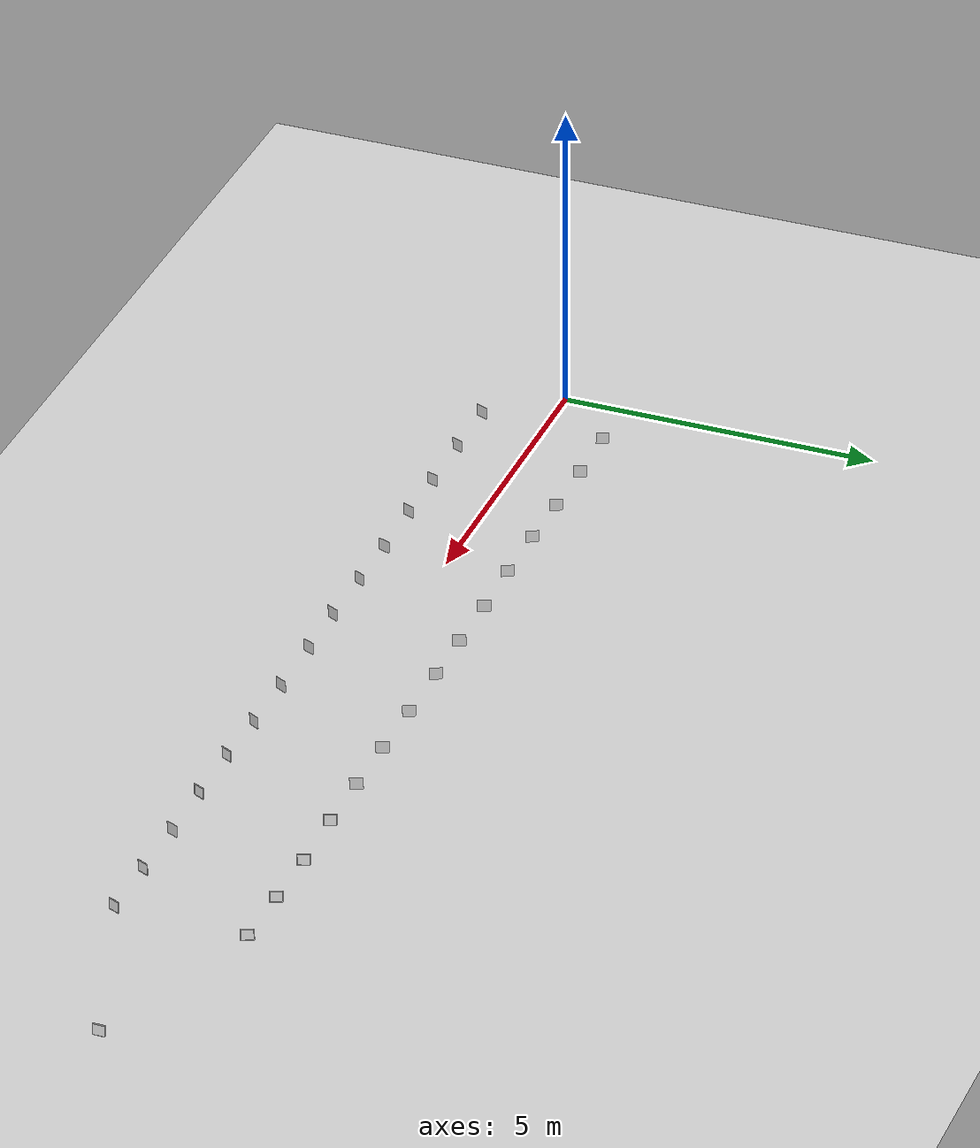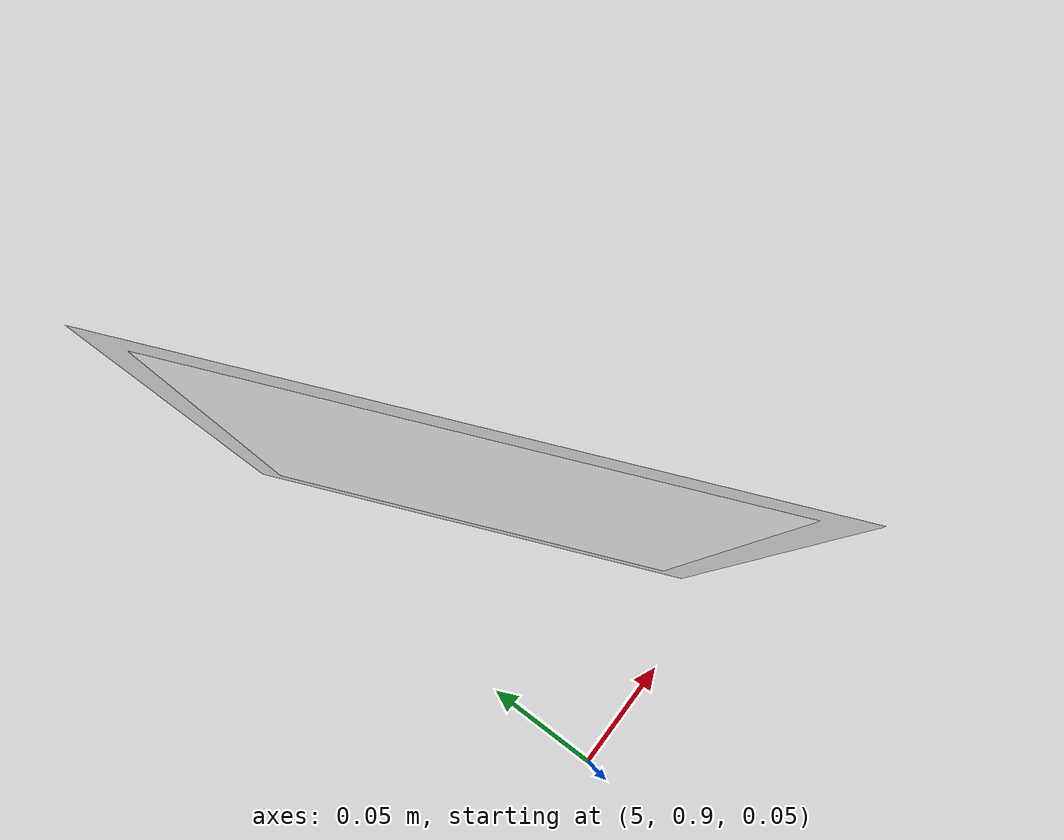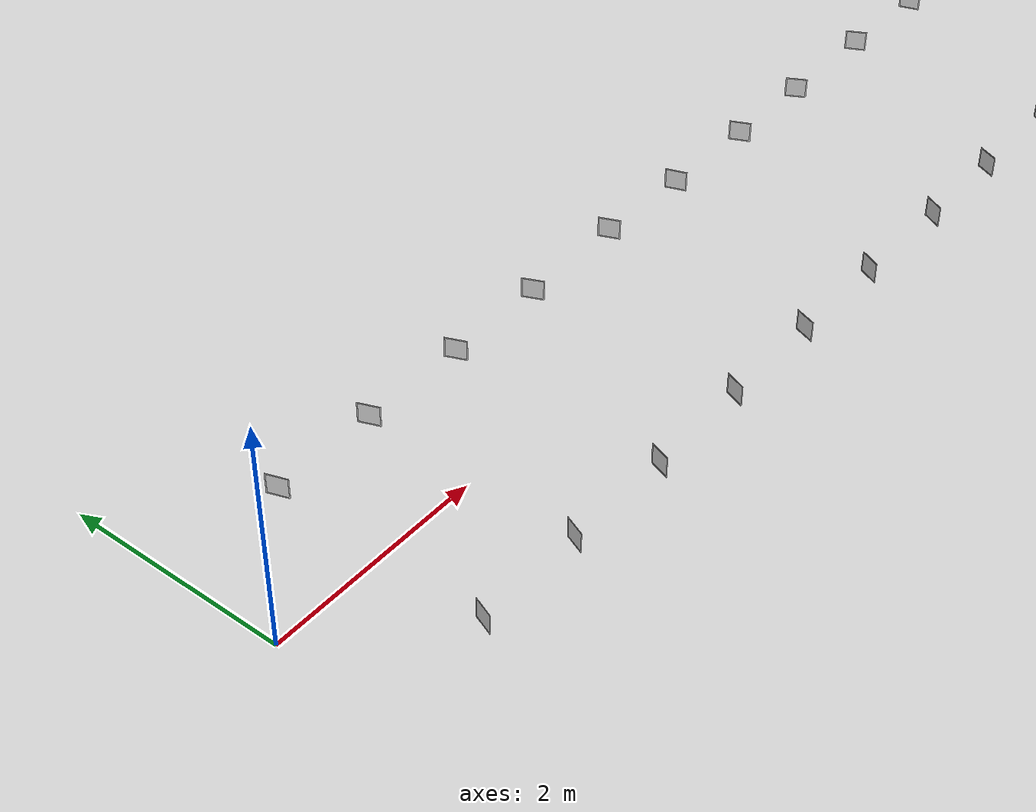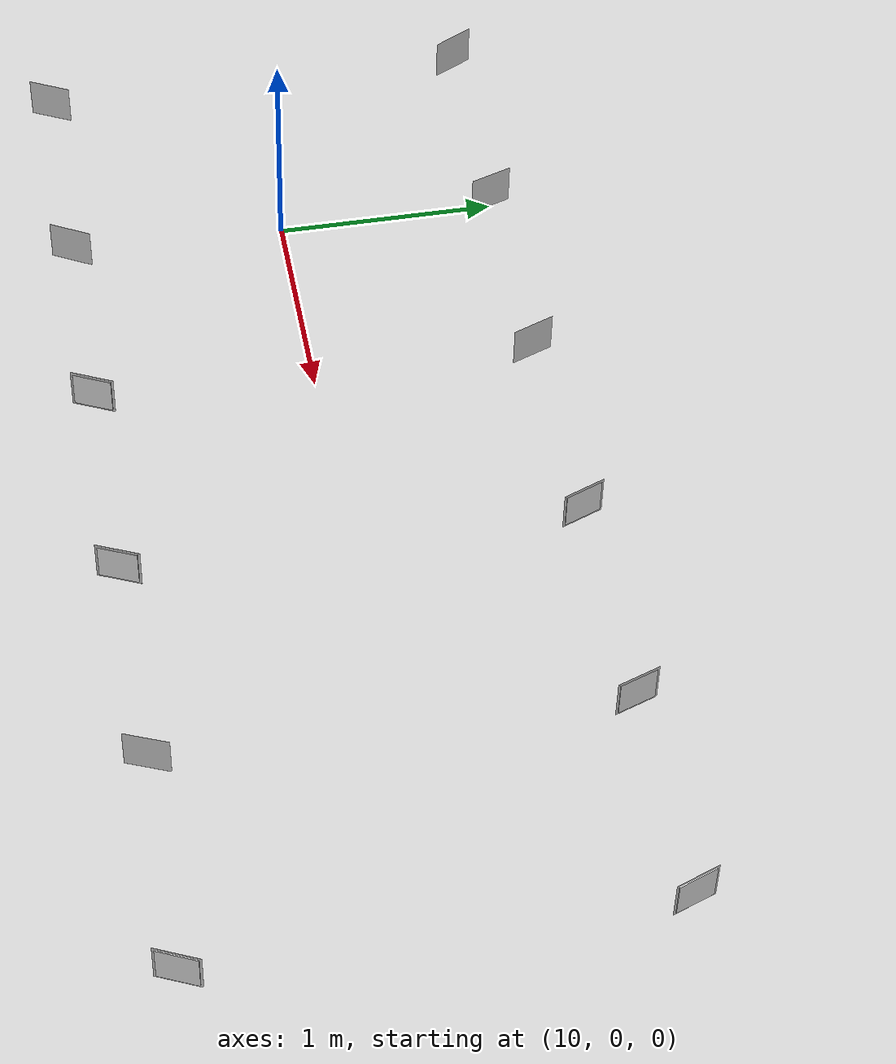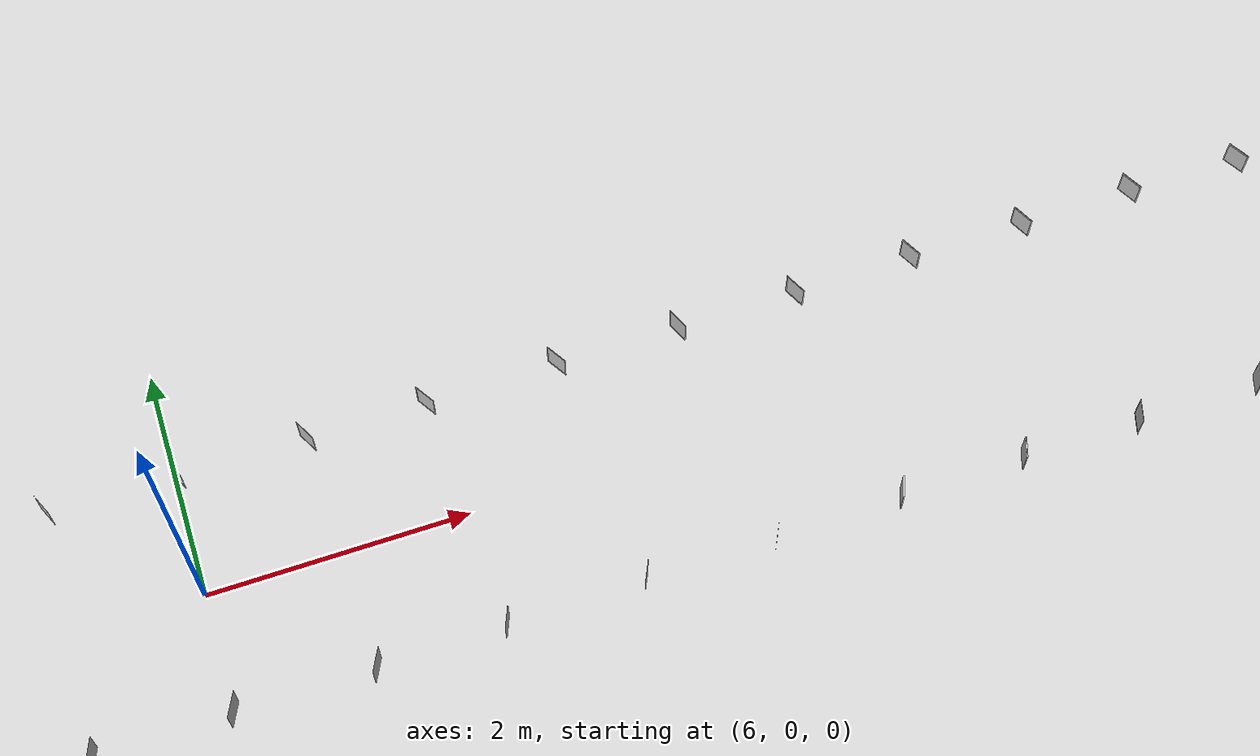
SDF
<sdf version="1.7">
 <world name="default">
  <light name="sun" type="directional">
   <pose>0 0 10 0 -0 0</pose>
   <diffuse>0.8 0.8 0.8 1</diffuse>
   <specular>0.2 0.2 0.2 1</specular>
   <attenuation>
    <range>1000</range>
    <constant>0.9</constant>
    <linear>0.01</linear>
    <quadratic>0.001</quadratic>
   </attenuation>
   <direction>-0.5 0.1 -0.9</direction>
   <spot><inner_angle>0</inner_angle><outer_angle>0</outer_angle><falloff>0</falloff></spot>
  </light>
  <model name="ground_plane">
   <pose>-4.80524 -1.20681 0 0 -0 0</pose>
   <static>1</static>
   <link name="link">
    <collision name="collision">
     <geometry><plane><normal>0 0 1</normal><size>100 100</size></plane></geometry>
     <surface>
      <contact><collide_bitmask>65535</collide_bitmask></contact>
      <friction><ode><mu>100</mu><mu2>50</mu2></ode></friction>
     </surface>
    </collision>
    <visual name="visual">
     <cast_shadows>0</cast_shadows>
     <geometry><plane><normal>0 0 1</normal><size>100 100</size></plane></geometry>
     <material>
      <script><uri>file://media/materials/scripts/gazebo.material</uri><name>Gazebo/Grey</name></script>
     </material>
    </visual>
   </link>
  </model>
  <model name="aruco_visual_marker_1_0">
   <link name="marker">
    <gravity>0</gravity>
    <visual name="visual">
     <geometry><box><size>0.1778 0.1778 0</size></box></geometry>
     <material>
      <script>
       <uri>model://aruco_visual_marker_1/materials/scripts</uri>
       <uri>model://aruco_visual_marker_1/materials/textures</uri>
       <name>ArucoVisualMarker1/Marker</name>
      </script>
      <ambient>1 1 1 1</ambient>
      <diffuse>1 1 1 1</diffuse>
      <specular>0 0 0 1</specular>
      <emissive>1 1 1 0</emissive>
      <shader type="vertex"><normal_map>__default__</normal_map></shader>
     </material>
    </visual>
   </link>
   <link name="marker_pad">
    <gravity>0</gravity>
    <pose relative_to="marker">0 0 -1e-05 0 -0 0</pose>
    <visual name="visual">
     <geometry><box><size>0.2 0.2 0</size></box></geometry>
     <material>
      <lighting>1</lighting>
      <script><uri>file://media/materials/scripts/gazebo.material</uri><name>Gazebo/White</name></script>
      <ambient>0.3 0.3 0.3 1</ambient>
      <diffuse>0.7 0.7 0.7 1</diffuse>
      <specular>0.01 0.01 0.01 1</specular>
      <emissive>1 1 1 0</emissive>
      <shader type="vertex"><normal_map>__default__</normal_map></shader>
     </material>
    </visual>
   </link>
   <joint name="marker_JOINT_marker_pad" type="revolute">
    <parent>marker</parent>
    <child>marker_pad</child>
    <axis>
     <xyz>0 0 1</xyz>
     <limit><upper>0</upper><lower>0</lower></limit>
     <dynamics><spring_reference>0</spring_reference><spring_stiffness>0</spring_stiffness></dynamics>
    </axis>
   </joint>
   <static>0</static>
   <pose>1.0316 0.995029 0.122107 0.342859 -1.56914 1e-06</pose>
  </model>
  <model name="aruco_visual_marker_3_0">
   <link name="marker">
    <gravity>0</gravity>
    <visual name="visual">
     <geometry><box><size>0.1778 0.1778 0</size></box></geometry>
     <material>
      <script>
       <uri>model://aruco_visual_marker_3/materials/scripts</uri>
       <uri>model://aruco_visual_marker_3/materials/textures</uri>
       <name>ArucoVisualMarker3/Marker</name>
      </script>
      <ambient>1 1 1 1</ambient>
      <diffuse>1 1 1 1</diffuse>
      <specular>0 0 0 1</specular>
      <emissive>1 1 1 0</emissive>
      <shader type="vertex"><normal_map>__default__</normal_map></shader>
     </material>
    </visual>
   </link>
   <link name="marker_pad">
    <gravity>0</gravity>
    <pose relative_to="marker">0 0 -1e-05 0 -0 0</pose>
    <visual name="visual">
     <geometry><box><size>0.2 0.2 0</size></box></geometry>
     <material>
      <lighting>1</lighting>
      <script><uri>file://media/materials/scripts/gazebo.material</uri><name>Gazebo/White</name></script>
      <ambient>0.3 0.3 0.3 1</ambient>
      <diffuse>0.7 0.7 0.7 1</diffuse>
      <specular>0.01 0.01 0.01 1</specular>
      <emissive>1 1 1 0</emissive>
      <shader type="vertex"><normal_map>__default__</normal_map></shader>
     </material>
    </visual>
   </link>
   <joint name="marker_JOINT_marker_pad" type="revolute">
    <parent>marker</parent>
    <child>marker_pad</child>
    <axis>
     <xyz>0 0 1</xyz>
     <limit><upper>0</upper><lower>0</lower></limit>
     <dynamics><spring_reference>0</spring_reference><spring_stiffness>0</spring_stiffness></dynamics>
    </axis>
   </joint>
   <static>0</static>
   <pose>2.03377 1.00703 0.117864 0.382875 -1.56691 -2e-06</pose>
  </model>
  <model name="aruco_visual_marker_5_0">
   <link name="marker">
    <gravity>0</gravity>
    <visual name="visual">
     <geometry><box><size>0.1778 0.1778 0</size></box></geometry>
     <material>
      <script>
       <uri>model://aruco_visual_marker_5/materials/scripts</uri>
       <uri>model://aruco_visual_marker_5/materials/textures</uri>
       <name>ArucoVisualMarker5/Marker</name>
      </script>
      <ambient>1 1 1 1</ambient>
      <diffuse>1 1 1 1</diffuse>
      <specular>0 0 0 1</specular>
      <emissive>1 1 1 0</emissive>
      <shader type="vertex"><normal_map>__default__</normal_map></shader>
     </material>
    </visual>
   </link>
   <link name="marker_pad">
    <gravity>0</gravity>
    <pose relative_to="marker">0 0 -1e-05 0 -0 0</pose>
    <visual name="visual">
     <geometry><box><size>0.2 0.2 0</size></box></geometry>
     <material>
      <lighting>1</lighting>
      <script><uri>file://media/materials/scripts/gazebo.material</uri><name>Gazebo/White</name></script>
      <ambient>0.3 0.3 0.3 1</ambient>
      <diffuse>0.7 0.7 0.7 1</diffuse>
      <specular>0.01 0.01 0.01 1</specular>
      <emissive>1 1 1 0</emissive>
      <shader type="vertex"><normal_map>__default__</normal_map></shader>
     </material>
    </visual>
   </link>
   <joint name="marker_JOINT_marker_pad" type="revolute">
    <parent>marker</parent>
    <child>marker_pad</child>
    <axis>
     <xyz>0 0 1</xyz>
     <limit><upper>0</upper><lower>0</lower></limit>
     <dynamics><spring_reference>0</spring_reference><spring_stiffness>0</spring_stiffness></dynamics>
    </axis>
   </joint>
   <static>0</static>
   <pose>3.04436 1.00176 0.112852 0.40147 -1.5682 9e-06</pose>
  </model>
  <model name="aruco_visual_marker_7_0">
   <link name="marker">
    <gravity>0</gravity>
    <visual name="visual">
     <geometry><box><size>0.1778 0.1778 0</size></box></geometry>
     <material>
      <script>
       <uri>model://aruco_visual_marker_7/materials/scripts</uri>
       <uri>model://aruco_visual_marker_7/materials/textures</uri>
       <name>ArucoVisualMarker7/Marker</name>
      </script>
      <ambient>1 1 1 1</ambient>
      <diffuse>1 1 1 1</diffuse>
      <specular>0 0 0 1</specular>
      <emissive>1 1 1 0</emissive>
      <shader type="vertex"><normal_map>__default__</normal_map></shader>
     </material>
    </visual>
   </link>
   <link name="marker_pad">
    <gravity>0</gravity>
    <pose relative_to="marker">0 0 -1e-05 0 -0 0</pose>
    <visual name="visual">
     <geometry><box><size>0.2 0.2 0</size></box></geometry>
     <material>
      <lighting>1</lighting>
      <script><uri>file://media/materials/scripts/gazebo.material</uri><name>Gazebo/White</name></script>
      <ambient>0.3 0.3 0.3 1</ambient>
      <diffuse>0.7 0.7 0.7 1</diffuse>
      <specular>0.01 0.01 0.01 1</specular>
      <emissive>1 1 1 0</emissive>
      <shader type="vertex"><normal_map>__default__</normal_map></shader>
     </material>
    </visual>
   </link>
   <joint name="marker_JOINT_marker_pad" type="revolute">
    <parent>marker</parent>
    <child>marker_pad</child>
    <axis>
     <xyz>0 0 1</xyz>
     <limit><upper>0</upper><lower>0</lower></limit>
     <dynamics><spring_reference>0</spring_reference><spring_stiffness>0</spring_stiffness></dynamics>
    </axis>
   </joint>
   <static>0</static>
   <pose>4.01192 0.997134 0.124609 -2.71837 -1.56706 3.14159</pose>
  </model>
  <model name="aruco_visual_marker_9_0">
   <link name="marker">
    <gravity>0</gravity>
    <visual name="visual">
     <geometry><box><size>0.1778 0.1778 0</size></box></geometry>
     <material>
      <script>
       <uri>model://aruco_visual_marker_9/materials/scripts</uri>
       <uri>model://aruco_visual_marker_9/materials/textures</uri>
       <name>ArucoVisualMarker9/Marker</name>
      </script>
      <ambient>1 1 1 1</ambient>
      <diffuse>1 1 1 1</diffuse>
      <specular>0 0 0 1</specular>
      <emissive>1 1 1 0</emissive>
      <shader type="vertex"><normal_map>__default__</normal_map></shader>
     </material>
    </visual>
   </link>
   <link name="marker_pad">
    <gravity>0</gravity>
    <pose relative_to="marker">0 0 -1e-05 0 -0 0</pose>
    <visual name="visual">
     <geometry><box><size>0.2 0.2 0</size></box></geometry>
     <material>
      <lighting>1</lighting>
      <script><uri>file://media/materials/scripts/gazebo.material</uri><name>Gazebo/White</name></script>
      <ambient>0.3 0.3 0.3 1</ambient>
      <diffuse>0.7 0.7 0.7 1</diffuse>
      <specular>0.01 0.01 0.01 1</specular>
      <emissive>1 1 1 0</emissive>
      <shader type="vertex"><normal_map>__default__</normal_map></shader>
     </material>
    </visual>
   </link>
   <joint name="marker_JOINT_marker_pad" type="revolute">
    <parent>marker</parent>
    <child>marker_pad</child>
    <axis>
     <xyz>0 0 1</xyz>
     <limit><upper>0</upper><lower>0</lower></limit>
     <dynamics><spring_reference>0</spring_reference><spring_stiffness>0</spring_stiffness></dynamics>
    </axis>
   </joint>
   <static>0</static>
   <pose>5.05214 1.00394 0.140601 -2.74064 -1.56688 -3.14159</pose>
  </model>
  <model name="aruco_visual_marker_11_0">
   <link name="marker">
    <gravity>0</gravity>
    <visual name="visual">
     <geometry><box><size>0.1778 0.1778 0</size></box></geometry>
     <material>
      <script>
       <uri>model://aruco_visual_marker_11/materials/scripts</uri>
       <uri>model://aruco_visual_marker_11/materials/textures</uri>
       <name>ArucoVisualMarker11/Marker</name>
      </script>
      <ambient>1 1 1 1</ambient>
      <diffuse>1 1 1 1</diffuse>
      <specular>0 0 0 1</specular>
      <emissive>1 1 1 0</emissive>
      <shader type="vertex"><normal_map>__default__</normal_map></shader>
     </material>
    </visual>
   </link>
   <link name="marker_pad">
    <gravity>0</gravity>
    <pose relative_to="marker">0 0 -1e-05 0 -0 0</pose>
    <visual name="visual">
     <geometry><box><size>0.2 0.2 0</size></box></geometry>
     <material>
      <lighting>1</lighting>
      <script><uri>file://media/materials/scripts/gazebo.material</uri><name>Gazebo/White</name></script>
      <ambient>0.3 0.3 0.3 1</ambient>
      <diffuse>0.7 0.7 0.7 1</diffuse>
      <specular>0.01 0.01 0.01 1</specular>
      <emissive>1 1 1 0</emissive>
      <shader type="vertex"><normal_map>__default__</normal_map></shader>
     </material>
    </visual>
   </link>
   <joint name="marker_JOINT_marker_pad" type="revolute">
    <parent>marker</parent>
    <child>marker_pad</child>
    <axis>
     <xyz>0 0 1</xyz>
     <limit><upper>0</upper><lower>0</lower></limit>
     <dynamics><spring_reference>0</spring_reference><spring_stiffness>0</spring_stiffness></dynamics>
    </axis>
   </joint>
   <static>0</static>
   <pose>6.02337 1.00369 0.109905 0.352438 -1.5683 -3e-06</pose>
  </model>
  <model name="aruco_visual_marker_13_0">
   <link name="marker">
    <gravity>0</gravity>
    <visual name="visual">
     <geometry><box><size>0.1778 0.1778 0</size></box></geometry>
     <material>
      <script>
       <uri>model://aruco_visual_marker_13/materials/scripts</uri>
       <uri>model://aruco_visual_marker_13/materials/textures</uri>
       <name>ArucoVisualMarker13/Marker</name>
      </script>
      <ambient>1 1 1 1</ambient>
      <diffuse>1 1 1 1</diffuse>
      <specular>0 0 0 1</specular>
      <emissive>1 1 1 0</emissive>
      <shader type="vertex"><normal_map>__default__</normal_map></shader>
     </material>
    </visual>
   </link>
   <link name="marker_pad">
    <gravity>0</gravity>
    <pose relative_to="marker">0 0 -1e-05 0 -0 0</pose>
    <visual name="visual">
     <geometry><box><size>0.2 0.2 0</size></box></geometry>
     <material>
      <lighting>1</lighting>
      <script><uri>file://media/materials/scripts/gazebo.material</uri><name>Gazebo/White</name></script>
      <ambient>0.3 0.3 0.3 1</ambient>
      <diffuse>0.7 0.7 0.7 1</diffuse>
      <specular>0.01 0.01 0.01 1</specular>
      <emissive>1 1 1 0</emissive>
      <shader type="vertex"><normal_map>__default__</normal_map></shader>
     </material>
    </visual>
   </link>
   <joint name="marker_JOINT_marker_pad" type="revolute">
    <parent>marker</parent>
    <child>marker_pad</child>
    <axis>
     <xyz>0 0 1</xyz>
     <limit><upper>0</upper><lower>0</lower></limit>
     <dynamics><spring_reference>0</spring_reference><spring_stiffness>0</spring_stiffness></dynamics>
    </axis>
   </joint>
   <static>0</static>
   <pose>7.01227 0.998366 0.109114 0.441306 -1.57028 5e-06</pose>
  </model>
  <model name="aruco_visual_marker_15_0">
   <link name="marker">
    <gravity>0</gravity>
    <visual name="visual">
     <geometry><box><size>0.1778 0.1778 0</size></box></geometry>
     <material>
      <script>
       <uri>model://aruco_visual_marker_15/materials/scripts</uri>
       <uri>model://aruco_visual_marker_15/materials/textures</uri>
       <name>ArucoVisualMarker15/Marker</name>
      </script>
      <ambient>1 1 1 1</ambient>
      <diffuse>1 1 1 1</diffuse>
      <specular>0 0 0 1</specular>
      <emissive>1 1 1 0</emissive>
      <shader type="vertex"><normal_map>__default__</normal_map></shader>
     </material>
    </visual>
   </link>
   <link name="marker_pad">
    <gravity>0</gravity>
    <pose relative_to="marker">0 0 -1e-05 0 -0 0</pose>
    <visual name="visual">
     <geometry><box><size>0.2 0.2 0</size></box></geometry>
     <material>
      <lighting>1</lighting>
      <script><uri>file://media/materials/scripts/gazebo.material</uri><name>Gazebo/White</name></script>
      <ambient>0.3 0.3 0.3 1</ambient>
      <diffuse>0.7 0.7 0.7 1</diffuse>
      <specular>0.01 0.01 0.01 1</specular>
      <emissive>1 1 1 0</emissive>
      <shader type="vertex"><normal_map>__default__</normal_map></shader>
     </material>
    </visual>
   </link>
   <joint name="marker_JOINT_marker_pad" type="revolute">
    <parent>marker</parent>
    <child>marker_pad</child>
    <axis>
     <xyz>0 0 1</xyz>
     <limit><upper>0</upper><lower>0</lower></limit>
     <dynamics><spring_reference>0</spring_reference><spring_stiffness>0</spring_stiffness></dynamics>
    </axis>
   </joint>
   <static>0</static>
   <pose>7.95057 1.00409 0.106485 0.501669 -1.56985 3e-06</pose>
  </model>
  <model name="aruco_visual_marker_17_0">
   <link name="marker">
    <gravity>0</gravity>
    <visual name="visual">
     <geometry><box><size>0.1778 0.1778 0</size></box></geometry>
     <material>
      <script>
       <uri>model://aruco_visual_marker_17/materials/scripts</uri>
       <uri>model://aruco_visual_marker_17/materials/textures</uri>
       <name>ArucoVisualMarker17/Marker</name>
      </script>
      <ambient>1 1 1 1</ambient>
      <diffuse>1 1 1 1</diffuse>
      <specular>0 0 0 1</specular>
      <emissive>1 1 1 0</emissive>
      <shader type="vertex"><normal_map>__default__</normal_map></shader>
     </material>
    </visual>
   </link>
   <link name="marker_pad">
    <gravity>0</gravity>
    <pose relative_to="marker">0 0 -1e-05 0 -0 0</pose>
    <visual name="visual">
     <geometry><box><size>0.2 0.2 0</size></box></geometry>
     <material>
      <lighting>1</lighting>
      <script><uri>file://media/materials/scripts/gazebo.material</uri><name>Gazebo/White</name></script>
      <ambient>0.3 0.3 0.3 1</ambient>
      <diffuse>0.7 0.7 0.7 1</diffuse>
      <specular>0.01 0.01 0.01 1</specular>
      <emissive>1 1 1 0</emissive>
      <shader type="vertex"><normal_map>__default__</normal_map></shader>
     </material>
    </visual>
   </link>
   <joint name="marker_JOINT_marker_pad" type="revolute">
    <parent>marker</parent>
    <child>marker_pad</child>
    <axis>
     <xyz>0 0 1</xyz>
     <limit><upper>0</upper><lower>0</lower></limit>
     <dynamics><spring_reference>0</spring_reference><spring_stiffness>0</spring_stiffness></dynamics>
    </axis>
   </joint>
   <static>0</static>
   <pose>9.00818 1.00721 0.117547 0.481715 -1.56664 0</pose>
  </model>
  <model name="aruco_visual_marker_2_0">
   <link name="marker">
    <gravity>0</gravity>
    <visual name="visual">
     <geometry><box><size>0.1778 0.1778 0</size></box></geometry>
     <material>
      <script>
       <uri>model://aruco_visual_marker_2/materials/scripts</uri>
       <uri>model://aruco_visual_marker_2/materials/textures</uri>
       <name>ArucoVisualMarker2/Marker</name>
      </script>
      <ambient>1 1 1 1</ambient>
      <diffuse>1 1 1 1</diffuse>
      <specular>0 0 0 1</specular>
      <emissive>1 1 1 0</emissive>
      <shader type="vertex"><normal_map>__default__</normal_map></shader>
     </material>
    </visual>
   </link>
   <link name="marker_pad">
    <gravity>0</gravity>
    <pose relative_to="marker">0 0 -1e-05 0 -0 0</pose>
    <visual name="visual">
     <geometry><box><size>0.2 0.2 0</size></box></geometry>
     <material>
      <lighting>1</lighting>
      <script><uri>file://media/materials/scripts/gazebo.material</uri><name>Gazebo/White</name></script>
      <ambient>0.3 0.3 0.3 1</ambient>
      <diffuse>0.7 0.7 0.7 1</diffuse>
      <specular>0.01 0.01 0.01 1</specular>
      <emissive>1 1 1 0</emissive>
      <shader type="vertex"><normal_map>__default__</normal_map></shader>
     </material>
    </visual>
   </link>
   <joint name="marker_JOINT_marker_pad" type="revolute">
    <parent>marker</parent>
    <child>marker_pad</child>
    <axis>
     <xyz>0 0 1</xyz>
     <limit><upper>0</upper><lower>0</lower></limit>
     <dynamics><spring_reference>0</spring_reference><spring_stiffness>0</spring_stiffness></dynamics>
    </axis>
   </joint>
   <static>0</static>
   <pose>0.993199 -1.00067 0.133562 -0.361848 -1.56978 1.4e-05</pose>
  </model>
  <model name="aruco_visual_marker_4_0">
   <link name="marker">
    <gravity>0</gravity>
    <visual name="visual">
     <geometry><box><size>0.1778 0.1778 0</size></box></geometry>
     <material>
      <script>
       <uri>model://aruco_visual_marker_4/materials/scripts</uri>
       <uri>model://aruco_visual_marker_4/materials/textures</uri>
       <name>ArucoVisualMarker4/Marker</name>
      </script>
      <ambient>1 1 1 1</ambient>
      <diffuse>1 1 1 1</diffuse>
      <specular>0 0 0 1</specular>
      <emissive>1 1 1 0</emissive>
      <shader type="vertex"><normal_map>__default__</normal_map></shader>
     </material>
    </visual>
   </link>
   <link name="marker_pad">
    <gravity>0</gravity>
    <pose relative_to="marker">0 0 -1e-05 0 -0 0</pose>
    <visual name="visual">
     <geometry><box><size>0.2 0.2 0</size></box></geometry>
     <material>
      <lighting>1</lighting>
      <script><uri>file://media/materials/scripts/gazebo.material</uri><name>Gazebo/White</name></script>
      <ambient>0.3 0.3 0.3 1</ambient>
      <diffuse>0.7 0.7 0.7 1</diffuse>
      <specular>0.01 0.01 0.01 1</specular>
      <emissive>1 1 1 0</emissive>
      <shader type="vertex"><normal_map>__default__</normal_map></shader>
     </material>
    </visual>
   </link>
   <joint name="marker_JOINT_marker_pad" type="revolute">
    <parent>marker</parent>
    <child>marker_pad</child>
    <axis>
     <xyz>0 0 1</xyz>
     <limit><upper>0</upper><lower>0</lower></limit>
     <dynamics><spring_reference>0</spring_reference><spring_stiffness>0</spring_stiffness></dynamics>
    </axis>
   </joint>
   <static>0</static>
   <pose>2.00631 -1.00088 0.118381 -0.386754 -1.57066 -1.9e-05</pose>
  </model>
  <model name="aruco_visual_marker_8_0">
   <link name="marker">
    <gravity>0</gravity>
    <visual name="visual">
     <geometry><box><size>0.1778 0.1778 0</size></box></geometry>
     <material>
      <script>
       <uri>model://aruco_visual_marker_8/materials/scripts</uri>
       <uri>model://aruco_visual_marker_8/materials/textures</uri>
       <name>ArucoVisualMarker8/Marker</name>
      </script>
      <ambient>1 1 1 1</ambient>
      <diffuse>1 1 1 1</diffuse>
      <specular>0 0 0 1</specular>
      <emissive>1 1 1 0</emissive>
      <shader type="vertex"><normal_map>__default__</normal_map></shader>
     </material>
    </visual>
   </link>
   <link name="marker_pad">
    <gravity>0</gravity>
    <pose relative_to="marker">0 0 -1e-05 0 -0 0</pose>
    <visual name="visual">
     <geometry><box><size>0.2 0.2 0</size></box></geometry>
     <material>
      <lighting>1</lighting>
      <script><uri>file://media/materials/scripts/gazebo.material</uri><name>Gazebo/White</name></script>
      <ambient>0.3 0.3 0.3 1</ambient>
      <diffuse>0.7 0.7 0.7 1</diffuse>
      <specular>0.01 0.01 0.01 1</specular>
      <emissive>1 1 1 0</emissive>
      <shader type="vertex"><normal_map>__default__</normal_map></shader>
     </material>
    </visual>
   </link>
   <joint name="marker_JOINT_marker_pad" type="revolute">
    <parent>marker</parent>
    <child>marker_pad</child>
    <axis>
     <xyz>0 0 1</xyz>
     <limit><upper>0</upper><lower>0</lower></limit>
     <dynamics><spring_reference>0</spring_reference><spring_stiffness>0</spring_stiffness></dynamics>
    </axis>
   </joint>
   <static>0</static>
   <pose>4.01424 -1.00172 0.127469 -1.2431 -1.56269 0.882332</pose>
  </model>
  <model name="aruco_visual_marker_10_0">
   <link name="marker">
    <gravity>0</gravity>
    <visual name="visual">
     <geometry><box><size>0.1778 0.1778 0</size></box></geometry>
     <material>
      <script>
       <uri>model://aruco_visual_marker_10/materials/scripts</uri>
       <uri>model://aruco_visual_marker_10/materials/textures</uri>
       <name>ArucoVisualMarker10/Marker</name>
      </script>
      <ambient>1 1 1 1</ambient>
      <diffuse>1 1 1 1</diffuse>
      <specular>0 0 0 1</specular>
      <emissive>1 1 1 0</emissive>
      <shader type="vertex"><normal_map>__default__</normal_map></shader>
     </material>
    </visual>
   </link>
   <link name="marker_pad">
    <gravity>0</gravity>
    <pose relative_to="marker">0 0 -1e-05 0 -0 0</pose>
    <visual name="visual">
     <geometry><box><size>0.2 0.2 0</size></box></geometry>
     <material>
      <lighting>1</lighting>
      <script><uri>file://media/materials/scripts/gazebo.material</uri><name>Gazebo/White</name></script>
      <ambient>0.3 0.3 0.3 1</ambient>
      <diffuse>0.7 0.7 0.7 1</diffuse>
      <specular>0.01 0.01 0.01 1</specular>
      <emissive>1 1 1 0</emissive>
      <shader type="vertex"><normal_map>__default__</normal_map></shader>
     </material>
    </visual>
   </link>
   <joint name="marker_JOINT_marker_pad" type="revolute">
    <parent>marker</parent>
    <child>marker_pad</child>
    <axis>
     <xyz>0 0 1</xyz>
     <limit><upper>0</upper><lower>0</lower></limit>
     <dynamics><spring_reference>0</spring_reference><spring_stiffness>0</spring_stiffness></dynamics>
    </axis>
   </joint>
   <static>0</static>
   <pose>5.02707 -0.98677 0.111411 2.80965 -1.57027 3.14158</pose>
  </model>
  <model name="aruco_visual_marker_12_0">
   <link name="marker">
    <gravity>0</gravity>
    <visual name="visual">
     <geometry><box><size>0.1778 0.1778 0</size></box></geometry>
     <material>
      <script>
       <uri>model://aruco_visual_marker_12/materials/scripts</uri>
       <uri>model://aruco_visual_marker_12/materials/textures</uri>
       <name>ArucoVisualMarker12/Marker</name>
      </script>
      <ambient>1 1 1 1</ambient>
      <diffuse>1 1 1 1</diffuse>
      <specular>0 0 0 1</specular>
      <emissive>1 1 1 0</emissive>
      <shader type="vertex"><normal_map>__default__</normal_map></shader>
     </material>
    </visual>
   </link>
   <link name="marker_pad">
    <gravity>0</gravity>
    <pose relative_to="marker">0 0 -1e-05 0 -0 0</pose>
    <visual name="visual">
     <geometry><box><size>0.2 0.2 0</size></box></geometry>
     <material>
      <lighting>1</lighting>
      <script><uri>file://media/materials/scripts/gazebo.material</uri><name>Gazebo/White</name></script>
      <ambient>0.3 0.3 0.3 1</ambient>
      <diffuse>0.7 0.7 0.7 1</diffuse>
      <specular>0.01 0.01 0.01 1</specular>
      <emissive>1 1 1 0</emissive>
      <shader type="vertex"><normal_map>__default__</normal_map></shader>
     </material>
    </visual>
   </link>
   <joint name="marker_JOINT_marker_pad" type="revolute">
    <parent>marker</parent>
    <child>marker_pad</child>
    <axis>
     <xyz>0 0 1</xyz>
     <limit><upper>0</upper><lower>0</lower></limit>
     <dynamics><spring_reference>0</spring_reference><spring_stiffness>0</spring_stiffness></dynamics>
    </axis>
   </joint>
   <static>0</static>
   <pose>6.00288 -0.98771 0.117307 2.71576 -1.56866 3.14159</pose>
  </model>
  <model name="aruco_visual_marker_14_0">
   <link name="marker">
    <gravity>0</gravity>
    <visual name="visual">
     <geometry><box><size>0.1778 0.1778 0</size></box></geometry>
     <material>
      <script>
       <uri>model://aruco_visual_marker_14/materials/scripts</uri>
       <uri>model://aruco_visual_marker_14/materials/textures</uri>
       <name>ArucoVisualMarker14/Marker</name>
      </script>
      <ambient>1 1 1 1</ambient>
      <diffuse>1 1 1 1</diffuse>
      <specular>0 0 0 1</specular>
      <emissive>1 1 1 0</emissive>
      <shader type="vertex"><normal_map>__default__</normal_map></shader>
     </material>
    </visual>
   </link>
   <link name="marker_pad">
    <gravity>0</gravity>
    <pose relative_to="marker">0 0 -1e-05 0 -0 0</pose>
    <visual name="visual">
     <geometry><box><size>0.2 0.2 0</size></box></geometry>
     <material>
      <lighting>1</lighting>
      <script><uri>file://media/materials/scripts/gazebo.material</uri><name>Gazebo/White</name></script>
      <ambient>0.3 0.3 0.3 1</ambient>
      <diffuse>0.7 0.7 0.7 1</diffuse>
      <specular>0.01 0.01 0.01 1</specular>
      <emissive>1 1 1 0</emissive>
      <shader type="vertex"><normal_map>__default__</normal_map></shader>
     </material>
    </visual>
   </link>
   <joint name="marker_JOINT_marker_pad" type="revolute">
    <parent>marker</parent>
    <child>marker_pad</child>
    <axis>
     <xyz>0 0 1</xyz>
     <limit><upper>0</upper><lower>0</lower></limit>
     <dynamics><spring_reference>0</spring_reference><spring_stiffness>0</spring_stiffness></dynamics>
    </axis>
   </joint>
   <static>0</static>
   <pose>7.02056 -1.00339 0.119956 -0.454639 -1.57064 -1.7e-05</pose>
  </model>
  <model name="aruco_visual_marker_16_0">
   <link name="marker">
    <gravity>0</gravity>
    <visual name="visual">
     <geometry><box><size>0.1778 0.1778 0</size></box></geometry>
     <material>
      <script>
       <uri>model://aruco_visual_marker_16/materials/scripts</uri>
       <uri>model://aruco_visual_marker_16/materials/textures</uri>
       <name>ArucoVisualMarker16/Marker</name>
      </script>
      <ambient>1 1 1 1</ambient>
      <diffuse>1 1 1 1</diffuse>
      <specular>0 0 0 1</specular>
      <emissive>1 1 1 0</emissive>
      <shader type="vertex"><normal_map>__default__</normal_map></shader>
     </material>
    </visual>
   </link>
   <link name="marker_pad">
    <gravity>0</gravity>
    <pose relative_to="marker">0 0 -1e-05 0 -0 0</pose>
    <visual name="visual">
     <geometry><box><size>0.2 0.2 0</size></box></geometry>
     <material>
      <lighting>1</lighting>
      <script><uri>file://media/materials/scripts/gazebo.material</uri><name>Gazebo/White</name></script>
      <ambient>0.3 0.3 0.3 1</ambient>
      <diffuse>0.7 0.7 0.7 1</diffuse>
      <specular>0.01 0.01 0.01 1</specular>
      <emissive>1 1 1 0</emissive>
      <shader type="vertex"><normal_map>__default__</normal_map></shader>
     </material>
    </visual>
   </link>
   <joint name="marker_JOINT_marker_pad" type="revolute">
    <parent>marker</parent>
    <child>marker_pad</child>
    <axis>
     <xyz>0 0 1</xyz>
     <limit><upper>0</upper><lower>0</lower></limit>
     <dynamics><spring_reference>0</spring_reference><spring_stiffness>0</spring_stiffness></dynamics>
    </axis>
   </joint>
   <static>0</static>
   <pose>7.97328 -0.997064 0.12018 2.74167 -1.56651 3.14159</pose>
  </model>
  <model name="aruco_visual_marker_18_0">
   <link name="marker">
    <gravity>0</gravity>
    <visual name="visual">
     <geometry><box><size>0.1778 0.1778 0</size></box></geometry>
     <material>
      <script>
       <uri>model://aruco_visual_marker_18/materials/scripts</uri>
       <uri>model://aruco_visual_marker_18/materials/textures</uri>
       <name>ArucoVisualMarker18/Marker</name>
      </script>
      <ambient>1 1 1 1</ambient>
      <diffuse>1 1 1 1</diffuse>
      <specular>0 0 0 1</specular>
      <emissive>1 1 1 0</emissive>
      <shader type="vertex"><normal_map>__default__</normal_map></shader>
     </material>
    </visual>
   </link>
   <link name="marker_pad">
    <gravity>0</gravity>
    <pose relative_to="marker">0 0 -1e-05 0 -0 0</pose>
    <visual name="visual">
     <geometry><box><size>0.2 0.2 0</size></box></geometry>
     <material>
      <lighting>1</lighting>
      <script><uri>file://media/materials/scripts/gazebo.material</uri><name>Gazebo/White</name></script>
      <ambient>0.3 0.3 0.3 1</ambient>
      <diffuse>0.7 0.7 0.7 1</diffuse>
      <specular>0.01 0.01 0.01 1</specular>
      <emissive>1 1 1 0</emissive>
      <shader type="vertex"><normal_map>__default__</normal_map></shader>
     </material>
    </visual>
   </link>
   <joint name="marker_JOINT_marker_pad" type="revolute">
    <parent>marker</parent>
    <child>marker_pad</child>
    <axis>
     <xyz>0 0 1</xyz>
     <limit><upper>0</upper><lower>0</lower></limit>
     <dynamics><spring_reference>0</spring_reference><spring_stiffness>0</spring_stiffness></dynamics>
    </axis>
   </joint>
   <static>0</static>
   <pose>9.02409 -0.990526 0.104002 -0.463369 -1.56852 -1e-06</pose>
  </model>
  <model name="aruco_visual_marker_20_0">
   <link name="marker">
    <gravity>0</gravity>
    <visual name="visual">
     <geometry><box><size>0.1778 0.1778 0</size></box></geometry>
     <material>
      <script>
       <uri>model://aruco_visual_marker_20/materials/scripts</uri>
       <uri>model://aruco_visual_marker_20/materials/textures</uri>
       <name>ArucoVisualMarker20/Marker</name>
      </script>
      <ambient>1 1 1 1</ambient>
      <diffuse>1 1 1 1</diffuse>
      <specular>0 0 0 1</specular>
      <emissive>1 1 1 0</emissive>
      <shader type="vertex"><normal_map>__default__</normal_map></shader>
     </material>
    </visual>
   </link>
   <link name="marker_pad">
    <gravity>0</gravity>
    <pose relative_to="marker">0 0 -1e-05 0 -0 0</pose>
    <visual name="visual">
     <geometry><box><size>0.2 0.2 0</size></box></geometry>
     <material>
      <lighting>1</lighting>
      <script><uri>file://media/materials/scripts/gazebo.material</uri><name>Gazebo/White</name></script>
      <ambient>0.3 0.3 0.3 1</ambient>
      <diffuse>0.7 0.7 0.7 1</diffuse>
      <specular>0.01 0.01 0.01 1</specular>
      <emissive>1 1 1 0</emissive>
      <shader type="vertex"><normal_map>__default__</normal_map></shader>
     </material>
    </visual>
   </link>
   <joint name="marker_JOINT_marker_pad" type="revolute">
    <parent>marker</parent>
    <child>marker_pad</child>
    <axis>
     <xyz>0 0 1</xyz>
     <limit><upper>0</upper><lower>0</lower></limit>
     <dynamics><spring_reference>0</spring_reference><spring_stiffness>0</spring_stiffness></dynamics>
    </axis>
   </joint>
   <static>0</static>
   <pose>10.0398 -0.995615 0.11011 2.64498 -1.56661 -3.14159</pose>
  </model>
  <model name="aruco_visual_marker_6_0">
   <link name="marker">
    <gravity>0</gravity>
    <visual name="visual">
     <geometry><box><size>0.1778 0.1778 0</size></box></geometry>
     <material>
      <script>
       <uri>model://aruco_visual_marker_6/materials/scripts</uri>
       <uri>model://aruco_visual_marker_6/materials/textures</uri>
       <name>ArucoVisualMarker6/Marker</name>
      </script>
      <ambient>1 1 1 1</ambient>
      <diffuse>1 1 1 1</diffuse>
      <specular>0 0 0 1</specular>
      <emissive>1 1 1 0</emissive>
      <shader type="vertex"><normal_map>__default__</normal_map></shader>
     </material>
    </visual>
   </link>
   <link name="marker_pad">
    <gravity>0</gravity>
    <pose relative_to="marker">0 0 -1e-05 0 -0 0</pose>
    <visual name="visual">
     <geometry><box><size>0.2 0.2 0</size></box></geometry>
     <material>
      <lighting>1</lighting>
      <script><uri>file://media/materials/scripts/gazebo.material</uri><name>Gazebo/White</name></script>
      <ambient>0.3 0.3 0.3 1</ambient>
      <diffuse>0.7 0.7 0.7 1</diffuse>
      <specular>0.01 0.01 0.01 1</specular>
      <emissive>1 1 1 0</emissive>
      <shader type="vertex"><normal_map>__default__</normal_map></shader>
     </material>
    </visual>
   </link>
   <joint name="marker_JOINT_marker_pad" type="revolute">
    <parent>marker</parent>
    <child>marker_pad</child>
    <axis>
     <xyz>0 0 1</xyz>
     <limit><upper>0</upper><lower>0</lower></limit>
     <dynamics><spring_reference>0</spring_reference><spring_stiffness>0</spring_stiffness></dynamics>
    </axis>
   </joint>
   <static>0</static>
   <pose>3.02562 -1.00612 0.103623 -0.331802 -1.56778 -2e-06</pose>
  </model>
  <model name="aruco_visual_marker_21_0">
   <link name="marker">
    <gravity>0</gravity>
    <visual name="visual">
     <geometry><box><size>0.1778 0.1778 0</size></box></geometry>
     <material>
      <script>
       <uri>model://aruco_visual_marker_21/materials/scripts</uri>
       <uri>model://aruco_visual_marker_21/materials/textures</uri>
       <name>ArucoVisualMarker21/Marker</name>
      </script>
      <ambient>1 1 1 1</ambient>
      <diffuse>1 1 1 1</diffuse>
      <specular>0 0 0 1</specular>
      <emissive>1 1 1 0</emissive>
      <shader type="vertex"><normal_map>__default__</normal_map></shader>
     </material>
    </visual>
   </link>
   <link name="marker_pad">
    <gravity>0</gravity>
    <pose relative_to="marker">0 0 -1e-05 0 -0 0</pose>
    <visual name="visual">
     <geometry><box><size>0.2 0.2 0</size></box></geometry>
     <material>
      <lighting>1</lighting>
      <script><uri>file://media/materials/scripts/gazebo.material</uri><name>Gazebo/White</name></script>
      <ambient>0.3 0.3 0.3 1</ambient>
      <diffuse>0.7 0.7 0.7 1</diffuse>
      <specular>0.01 0.01 0.01 1</specular>
      <emissive>1 1 1 0</emissive>
      <shader type="vertex"><normal_map>__default__</normal_map></shader>
     </material>
    </visual>
   </link>
   <joint name="marker_JOINT_marker_pad" type="revolute">
    <parent>marker</parent>
    <child>marker_pad</child>
    <axis>
     <xyz>0 0 1</xyz>
     <limit><upper>0</upper><lower>0</lower></limit>
     <dynamics><spring_reference>0</spring_reference><spring_stiffness>0</spring_stiffness></dynamics>
    </axis>
   </joint>
   <static>0</static>
   <pose>11.0094 0.996884 0.125617 0.365639 -1.56602 2e-06</pose>
  </model>
  <model name="aruco_visual_marker_19_0">
   <link name="marker">
    <gravity>0</gravity>
    <visual name="visual">
     <geometry><box><size>0.1778 0.1778 0</size></box></geometry>
     <material>
      <script>
       <uri>model://aruco_visual_marker_19/materials/scripts</uri>
       <uri>model://aruco_visual_marker_19/materials/textures</uri>
       <name>ArucoVisualMarker19/Marker</name>
      </script>
      <ambient>1 1 1 1</ambient>
      <diffuse>1 1 1 1</diffuse>
      <specular>0 0 0 1</specular>
      <emissive>1 1 1 0</emissive>
      <shader type="vertex"><normal_map>__default__</normal_map></shader>
     </material>
    </visual>
   </link>
   <link name="marker_pad">
    <gravity>0</gravity>
    <pose relative_to="marker">0 0 -1e-05 0 -0 0</pose>
    <visual name="visual">
     <geometry><box><size>0.2 0.2 0</size></box></geometry>
     <material>
      <lighting>1</lighting>
      <script><uri>file://media/materials/scripts/gazebo.material</uri><name>Gazebo/White</name></script>
      <ambient>0.3 0.3 0.3 1</ambient>
      <diffuse>0.7 0.7 0.7 1</diffuse>
      <specular>0.01 0.01 0.01 1</specular>
      <emissive>1 1 1 0</emissive>
      <shader type="vertex"><normal_map>__default__</normal_map></shader>
     </material>
    </visual>
   </link>
   <joint name="marker_JOINT_marker_pad" type="revolute">
    <parent>marker</parent>
    <child>marker_pad</child>
    <axis>
     <xyz>0 0 1</xyz>
     <limit><upper>0</upper><lower>0</lower></limit>
     <dynamics><spring_reference>0</spring_reference><spring_stiffness>0</spring_stiffness></dynamics>
    </axis>
   </joint>
   <static>0</static>
   <pose>10.0128 0.999565 0.120094 -2.81277 -1.569 3.14159</pose>
  </model>
  <model name="aruco_visual_marker_26_0">
   <link name="marker">
    <gravity>0</gravity>
    <visual name="visual">
     <geometry><box><size>0.1778 0.1778 0</size></box></geometry>
     <material>
      <script>
       <uri>model://aruco_visual_marker_26/materials/scripts</uri>
       <uri>model://aruco_visual_marker_26/materials/textures</uri>
       <name>ArucoVisualMarker26/Marker</name>
      </script>
      <ambient>1 1 1 1</ambient>
      <diffuse>1 1 1 1</diffuse>
      <specular>0 0 0 1</specular>
      <emissive>1 1 1 0</emissive>
      <shader type="vertex"><normal_map>__default__</normal_map></shader>
     </material>
    </visual>
   </link>
   <link name="marker_pad">
    <gravity>0</gravity>
    <pose relative_to="marker">0 0 -1e-05 0 -0 0</pose>
    <visual name="visual">
     <geometry><box><size>0.2 0.2 0</size></box></geometry>
     <material>
      <lighting>1</lighting>
      <script><uri>file://media/materials/scripts/gazebo.material</uri><name>Gazebo/White</name></script>
      <ambient>0.3 0.3 0.3 1</ambient>
      <diffuse>0.7 0.7 0.7 1</diffuse>
      <specular>0.01 0.01 0.01 1</specular>
      <emissive>1 1 1 0</emissive>
      <shader type="vertex"><normal_map>__default__</normal_map></shader>
     </material>
    </visual>
   </link>
   <joint name="marker_JOINT_marker_pad" type="revolute">
    <parent>marker</parent>
    <child>marker_pad</child>
    <axis>
     <xyz>0 0 1</xyz>
     <limit><upper>0</upper><lower>0</lower></limit>
     <dynamics><spring_reference>0</spring_reference><spring_stiffness>0</spring_stiffness></dynamics>
    </axis>
   </joint>
   <static>0</static>
   <pose>13.0075 -0.998435 0.13192 -0.385483 -1.56953 4e-06</pose>
  </model>
  <model name="aruco_visual_marker_27_0">
   <link name="marker">
    <gravity>0</gravity>
    <visual name="visual">
     <geometry><box><size>0.1778 0.1778 0.00980314</size></box></geometry>
     <material>
      <script>
       <uri>model://aruco_visual_marker_27/materials/scripts</uri>
       <uri>model://aruco_visual_marker_27/materials/textures</uri>
       <name>ArucoVisualMarker27/Marker</name>
      </script>
      <ambient>1 1 1 1</ambient>
      <diffuse>1 1 1 1</diffuse>
      <specular>0 0 0 1</specular>
      <emissive>1 1 1 0</emissive>
      <shader type="vertex"><normal_map>__default__</normal_map></shader>
     </material>
    </visual>
   </link>
   <link name="marker_pad">
    <gravity>0</gravity>
    <pose relative_to="marker">0 0 -1e-05 0 -0 0</pose>
    <visual name="visual">
     <geometry><box><size>0.2 0.2 0</size></box></geometry>
     <material>
      <lighting>1</lighting>
      <script><uri>file://media/materials/scripts/gazebo.material</uri><name>Gazebo/White</name></script>
      <ambient>0.3 0.3 0.3 1</ambient>
      <diffuse>0.7 0.7 0.7 1</diffuse>
      <specular>0.01 0.01 0.01 1</specular>
      <emissive>1 1 1 0</emissive>
      <shader type="vertex"><normal_map>__default__</normal_map></shader>
     </material>
    </visual>
   </link>
   <joint name="marker_JOINT_marker_pad" type="revolute">
    <parent>marker</parent>
    <child>marker_pad</child>
    <axis>
     <xyz>0 0 1</xyz>
     <limit><upper>0</upper><lower>0</lower></limit>
     <dynamics><spring_reference>0</spring_reference><spring_stiffness>0</spring_stiffness></dynamics>
    </axis>
   </joint>
   <static>0</static>
   <pose>14.0202 1.01739 0.149843 0.359145 -1.5678 -1e-06</pose>
  </model>
  <model name="aruco_visual_marker_22_0">
   <link name="marker">
    <gravity>0</gravity>
    <visual name="visual">
     <geometry><box><size>0.1778 0.1778 0.0108912</size></box></geometry>
     <material>
      <script>
       <uri>model://aruco_visual_marker_22/materials/scripts</uri>
       <uri>model://aruco_visual_marker_22/materials/textures</uri>
       <name>ArucoVisualMarker22/Marker</name>
      </script>
      <ambient>1 1 1 1</ambient>
      <diffuse>1 1 1 1</diffuse>
      <specular>0 0 0 1</specular>
      <emissive>1 1 1 0</emissive>
      <shader type="vertex"><normal_map>__default__</normal_map></shader>
     </material>
    </visual>
   </link>
   <link name="marker_pad">
    <gravity>0</gravity>
    <pose relative_to="marker">0 0 -1e-05 0 -0 0</pose>
    <visual name="visual">
     <geometry><box><size>0.2 0.2 0</size></box></geometry>
     <material>
      <lighting>1</lighting>
      <script><uri>file://media/materials/scripts/gazebo.material</uri><name>Gazebo/White</name></script>
      <ambient>0.3 0.3 0.3 1</ambient>
      <diffuse>0.7 0.7 0.7 1</diffuse>
      <specular>0.01 0.01 0.01 1</specular>
      <emissive>1 1 1 0</emissive>
      <shader type="vertex"><normal_map>__default__</normal_map></shader>
     </material>
    </visual>
   </link>
   <joint name="marker_JOINT_marker_pad" type="revolute">
    <parent>marker</parent>
    <child>marker_pad</child>
    <axis>
     <xyz>0 0 1</xyz>
     <limit><upper>0</upper><lower>0</lower></limit>
     <dynamics><spring_reference>0</spring_reference><spring_stiffness>0</spring_stiffness></dynamics>
    </axis>
   </joint>
   <static>0</static>
   <pose>11.0297 -0.998183 0.154531 -0.432741 -1.56929 -1e-06</pose>
  </model>
  <model name="aruco_visual_marker_24_0">
   <link name="marker">
    <gravity>0</gravity>
    <visual name="visual">
     <geometry><box><size>0.1778 0.1778 0.0100593</size></box></geometry>
     <material>
      <script>
       <uri>model://aruco_visual_marker_24/materials/scripts</uri>
       <uri>model://aruco_visual_marker_24/materials/textures</uri>
       <name>ArucoVisualMarker24/Marker</name>
      </script>
      <ambient>1 1 1 1</ambient>
      <diffuse>1 1 1 1</diffuse>
      <specular>0 0 0 1</specular>
      <emissive>1 1 1 0</emissive>
      <shader type="vertex"><normal_map>__default__</normal_map></shader>
     </material>
    </visual>
   </link>
   <link name="marker_pad">
    <gravity>0</gravity>
    <pose relative_to="marker">0 0 -1e-05 0 -0 0</pose>
    <visual name="visual">
     <geometry><box><size>0.2 0.2 0</size></box></geometry>
     <material>
      <lighting>1</lighting>
      <script><uri>file://media/materials/scripts/gazebo.material</uri><name>Gazebo/White</name></script>
      <ambient>0.3 0.3 0.3 1</ambient>
      <diffuse>0.7 0.7 0.7 1</diffuse>
      <specular>0.01 0.01 0.01 1</specular>
      <emissive>1 1 1 0</emissive>
      <shader type="vertex"><normal_map>__default__</normal_map></shader>
     </material>
    </visual>
   </link>
   <joint name="marker_JOINT_marker_pad" type="revolute">
    <parent>marker</parent>
    <child>marker_pad</child>
    <axis>
     <xyz>0 0 1</xyz>
     <limit><upper>0</upper><lower>0</lower></limit>
     <dynamics><spring_reference>0</spring_reference><spring_stiffness>0</spring_stiffness></dynamics>
    </axis>
   </joint>
   <static>0</static>
   <pose>12.0314 -0.999739 0.15207 -0.409114 -1.56845 7e-06</pose>
  </model>
  <model name="aruco_visual_marker_29_0">
   <link name="marker">
    <gravity>0</gravity>
    <visual name="visual">
     <geometry><box><size>0.1778 0.1778 0.0104107</size></box></geometry>
     <material>
      <script>
       <uri>model://aruco_visual_marker_29/materials/scripts</uri>
       <uri>model://aruco_visual_marker_29/materials/textures</uri>
       <name>ArucoVisualMarker29/Marker</name>
      </script>
      <ambient>1 1 1 1</ambient>
      <diffuse>1 1 1 1</diffuse>
      <specular>0 0 0 1</specular>
      <emissive>1 1 1 0</emissive>
      <shader type="vertex"><normal_map>__default__</normal_map></shader>
     </material>
    </visual>
   </link>
   <link name="marker_pad">
    <gravity>0</gravity>
    <pose relative_to="marker">0 0 -1e-05 0 -0 0</pose>
    <visual name="visual">
     <geometry><box><size>0.2 0.2 0</size></box></geometry>
     <material>
      <lighting>1</lighting>
      <script><uri>file://media/materials/scripts/gazebo.material</uri><name>Gazebo/White</name></script>
      <ambient>0.3 0.3 0.3 1</ambient>
      <diffuse>0.7 0.7 0.7 1</diffuse>
      <specular>0.01 0.01 0.01 1</specular>
      <emissive>1 1 1 0</emissive>
      <shader type="vertex"><normal_map>__default__</normal_map></shader>
     </material>
    </visual>
   </link>
   <joint name="marker_JOINT_marker_pad" type="revolute">
    <parent>marker</parent>
    <child>marker_pad</child>
    <axis>
     <xyz>0 0 1</xyz>
     <limit><upper>0</upper><lower>0</lower></limit>
     <dynamics><spring_reference>0</spring_reference><spring_stiffness>0</spring_stiffness></dynamics>
    </axis>
   </joint>
   <static>0</static>
   <pose>15.0131 0.99726 0.157088 -2.74609 -1.57079 3.14095</pose>
  </model>
  <model name="aruco_visual_marker_23_0">
   <link name="marker">
    <gravity>0</gravity>
    <visual name="visual">
     <geometry><box><size>0.1778 0.1778 0.00717313</size></box></geometry>
     <material>
      <script>
       <uri>model://aruco_visual_marker_23/materials/scripts</uri>
       <uri>model://aruco_visual_marker_23/materials/textures</uri>
       <name>ArucoVisualMarker23/Marker</name>
      </script>
      <ambient>1 1 1 1</ambient>
      <diffuse>1 1 1 1</diffuse>
      <specular>0 0 0 1</specular>
      <emissive>1 1 1 0</emissive>
      <shader type="vertex"><normal_map>__default__</normal_map></shader>
     </material>
    </visual>
   </link>
   <link name="marker_pad">
    <gravity>0</gravity>
    <pose relative_to="marker">0 0 -1e-05 0 -0 0</pose>
    <visual name="visual">
     <geometry><box><size>0.2 0.2 0</size></box></geometry>
     <material>
      <lighting>1</lighting>
      <script><uri>file://media/materials/scripts/gazebo.material</uri><name>Gazebo/White</name></script>
      <ambient>0.3 0.3 0.3 1</ambient>
      <diffuse>0.7 0.7 0.7 1</diffuse>
      <specular>0.01 0.01 0.01 1</specular>
      <emissive>1 1 1 0</emissive>
      <shader type="vertex"><normal_map>__default__</normal_map></shader>
     </material>
    </visual>
   </link>
   <joint name="marker_JOINT_marker_pad" type="revolute">
    <parent>marker</parent>
    <child>marker_pad</child>
    <axis>
     <xyz>0 0 1</xyz>
     <limit><upper>0</upper><lower>0</lower></limit>
     <dynamics><spring_reference>0</spring_reference><spring_stiffness>0</spring_stiffness></dynamics>
    </axis>
   </joint>
   <static>0</static>
   <pose>12.0176 1.00775 0.147017 0.37193 -1.56799 -3e-06</pose>
  </model>
  <model name="aruco_visual_marker_25_0">
   <link name="marker">
    <gravity>0</gravity>
    <visual name="visual">
     <geometry><box><size>0.1778 0.1778 0.00696459</size></box></geometry>
     <material>
      <script>
       <uri>model://aruco_visual_marker_25/materials/scripts</uri>
       <uri>model://aruco_visual_marker_25/materials/textures</uri>
       <name>ArucoVisualMarker25/Marker</name>
      </script>
      <ambient>1 1 1 1</ambient>
      <diffuse>1 1 1 1</diffuse>
      <specular>0 0 0 1</specular>
      <emissive>1 1 1 0</emissive>
      <shader type="vertex"><normal_map>__default__</normal_map></shader>
     </material>
    </visual>
   </link>
   <link name="marker_pad">
    <gravity>0</gravity>
    <pose relative_to="marker">0 0 -1e-05 0 -0 0</pose>
    <visual name="visual">
     <geometry><box><size>0.2 0.2 0</size></box></geometry>
     <material>
      <lighting>1</lighting>
      <script><uri>file://media/materials/scripts/gazebo.material</uri><name>Gazebo/White</name></script>
      <ambient>0.3 0.3 0.3 1</ambient>
      <diffuse>0.7 0.7 0.7 1</diffuse>
      <specular>0.01 0.01 0.01 1</specular>
      <emissive>1 1 1 0</emissive>
      <shader type="vertex"><normal_map>__default__</normal_map></shader>
     </material>
    </visual>
   </link>
   <joint name="marker_JOINT_marker_pad" type="revolute">
    <parent>marker</parent>
    <child>marker_pad</child>
    <axis>
     <xyz>0 0 1</xyz>
     <limit><upper>0</upper><lower>0</lower></limit>
     <dynamics><spring_reference>0</spring_reference><spring_stiffness>0</spring_stiffness></dynamics>
    </axis>
   </joint>
   <static>0</static>
   <pose>13.0266 1.01564 0.128533 -2.80083 -1.56718 -3.14159</pose>
  </model>
  <model name="aruco_visual_marker_28_0">
   <link name="marker">
    <gravity>0</gravity>
    <visual name="visual">
     <geometry><box><size>0.1778 0.1778 0.00963076</size></box></geometry>
     <material>
      <script>
       <uri>model://aruco_visual_marker_28/materials/scripts</uri>
       <uri>model://aruco_visual_marker_28/materials/textures</uri>
       <name>ArucoVisualMarker28/Marker</name>
      </script>
      <ambient>1 1 1 1</ambient>
      <diffuse>1 1 1 1</diffuse>
      <specular>0 0 0 1</specular>
      <emissive>1 1 1 0</emissive>
      <shader type="vertex"><normal_map>__default__</normal_map></shader>
     </material>
    </visual>
   </link>
   <link name="marker_pad">
    <gravity>0</gravity>
    <pose relative_to="marker">0 0 -1e-05 0 -0 0</pose>
    <visual name="visual">
     <geometry><box><size>0.2 0.2 0</size></box></geometry>
     <material>
      <lighting>1</lighting>
      <script><uri>file://media/materials/scripts/gazebo.material</uri><name>Gazebo/White</name></script>
      <ambient>0.3 0.3 0.3 1</ambient>
      <diffuse>0.7 0.7 0.7 1</diffuse>
      <specular>0.01 0.01 0.01 1</specular>
      <emissive>1 1 1 0</emissive>
      <shader type="vertex"><normal_map>__default__</normal_map></shader>
     </material>
    </visual>
   </link>
   <joint name="marker_JOINT_marker_pad" type="revolute">
    <parent>marker</parent>
    <child>marker_pad</child>
    <axis>
     <xyz>0 0 1</xyz>
     <limit><upper>0</upper><lower>0</lower></limit>
     <dynamics><spring_reference>0</spring_reference><spring_stiffness>0</spring_stiffness></dynamics>
    </axis>
   </joint>
   <static>0</static>
   <pose>14.0326 -1.00409 0.145168 -0.419555 -1.57051 4.3e-05</pose>
  </model>
  <model name="aruco_visual_marker_30_0">
   <link name="marker">
    <gravity>0</gravity>
    <visual name="visual">
     <geometry><box><size>0.1778 0.1778 0.0124206</size></box></geometry>
     <material>
      <script>
       <uri>model://aruco_visual_marker_30/materials/scripts</uri>
       <uri>model://aruco_visual_marker_30/materials/textures</uri>
       <name>ArucoVisualMarker30/Marker</name>
      </script>
      <ambient>1 1 1 1</ambient>
      <diffuse>1 1 1 1</diffuse>
      <specular>0 0 0 1</specular>
      <emissive>1 1 1 0</emissive>
      <shader type="vertex"><normal_map>__default__</normal_map></shader>
     </material>
    </visual>
   </link>
   <link name="marker_pad">
    <gravity>0</gravity>
    <pose relative_to="marker">0 0 -1e-05 0 -0 0</pose>
    <visual name="visual">
     <geometry><box><size>0.2 0.2 0</size></box></geometry>
     <material>
      <lighting>1</lighting>
      <script><uri>file://media/materials/scripts/gazebo.material</uri><name>Gazebo/White</name></script>
      <ambient>0.3 0.3 0.3 1</ambient>
      <diffuse>0.7 0.7 0.7 1</diffuse>
      <specular>0.01 0.01 0.01 1</specular>
      <emissive>1 1 1 0</emissive>
      <shader type="vertex"><normal_map>__default__</normal_map></shader>
     </material>
    </visual>
   </link>
   <joint name="marker_JOINT_marker_pad" type="revolute">
    <parent>marker</parent>
    <child>marker_pad</child>
    <axis>
     <xyz>0 0 1</xyz>
     <limit><upper>0</upper><lower>0</lower></limit>
     <dynamics><spring_reference>0</spring_reference><spring_stiffness>0</spring_stiffness></dynamics>
    </axis>
   </joint>
   <static>0</static>
   <pose>15.0332 -1.00679 0.154637 -0.380272 -1.56728 1e-06</pose>
  </model>
  <model name="aruco_visual_marker_1">
   <link name="marker">
    <gravity>0</gravity>
    <visual name="visual">
     <geometry><box><size>0.1778 0.1778 0</size></box></geometry>
     <material>
      <script>
       <uri>model://aruco_visual_marker_1/materials/scripts</uri>
       <uri>model://aruco_visual_marker_1/materials/textures</uri>
       <name>ArucoVisualMarker1/Marker</name>
      </script>
      <ambient>1 1 1 1</ambient>
      <diffuse>1 1 1 1</diffuse>
      <specular>0 0 0 1</specular>
      <emissive>1 1 1 0</emissive>
      <shader type="vertex"><normal_map>__default__</normal_map></shader>
     </material>
    </visual>
   </link>
   <link name="marker_pad">
    <gravity>0</gravity>
    <pose relative_to="marker">0 0 -1e-05 0 -0 0</pose>
    <visual name="visual">
     <geometry><box><size>0.2 0.2 0</size></box></geometry>
     <material>
      <lighting>1</lighting>
      <script><uri>file://media/materials/scripts/gazebo.material</uri><name>Gazebo/White</name></script>
      <ambient>0.3 0.3 0.3 1</ambient>
      <diffuse>0.7 0.7 0.7 1</diffuse>
      <specular>0.01 0.01 0.01 1</specular>
      <emissive>1 1 1 0</emissive>
      <shader type="vertex"><normal_map>__default__</normal_map></shader>
     </material>
    </visual>
   </link>
   <joint name="marker_JOINT_marker_pad" type="revolute">
    <parent>marker</parent>
    <child>marker_pad</child>
    <axis>
     <xyz>0 0 1</xyz>
     <limit><upper>0</upper><lower>0</lower></limit>
     <dynamics><spring_reference>0</spring_reference><spring_stiffness>0</spring_stiffness></dynamics>
    </axis>
   </joint>
   <static>0</static>
   <pose>1.0316 0.995029 0.122107 0.342859 -1.56914 1e-06</pose>
  </model>
  <model name="aruco_visual_marker_3">
   <link name="marker">
    <gravity>0</gravity>
    <visual name="visual">
     <geometry><box><size>0.1778 0.1778 0</size></box></geometry>
     <material>
      <script>
       <uri>model://aruco_visual_marker_3/materials/scripts</uri>
       <uri>model://aruco_visual_marker_3/materials/textures</uri>
       <name>ArucoVisualMarker3/Marker</name>
      </script>
      <ambient>1 1 1 1</ambient>
      <diffuse>1 1 1 1</diffuse>
      <specular>0 0 0 1</specular>
      <emissive>1 1 1 0</emissive>
      <shader type="vertex"><normal_map>__default__</normal_map></shader>
     </material>
    </visual>
   </link>
   <link name="marker_pad">
    <gravity>0</gravity>
    <pose relative_to="marker">0 0 -1e-05 0 -0 0</pose>
    <visual name="visual">
     <geometry><box><size>0.2 0.2 0</size></box></geometry>
     <material>
      <lighting>1</lighting>
      <script><uri>file://media/materials/scripts/gazebo.material</uri><name>Gazebo/White</name></script>
      <ambient>0.3 0.3 0.3 1</ambient>
      <diffuse>0.7 0.7 0.7 1</diffuse>
      <specular>0.01 0.01 0.01 1</specular>
      <emissive>1 1 1 0</emissive>
      <shader type="vertex"><normal_map>__default__</normal_map></shader>
     </material>
    </visual>
   </link>
   <joint name="marker_JOINT_marker_pad" type="revolute">
    <parent>marker</parent>
    <child>marker_pad</child>
    <axis>
     <xyz>0 0 1</xyz>
     <limit><upper>0</upper><lower>0</lower></limit>
     <dynamics><spring_reference>0</spring_reference><spring_stiffness>0</spring_stiffness></dynamics>
    </axis>
   </joint>
   <static>0</static>
   <pose>2.03377 1.00703 0.117864 0.382875 -1.56691 -2e-06</pose>
  </model>
  <model name="aruco_visual_marker_5">
   <link name="marker">
    <gravity>0</gravity>
    <visual name="visual">
     <geometry><box><size>0.1778 0.1778 0</size></box></geometry>
     <material>
      <script>
       <uri>model://aruco_visual_marker_5/materials/scripts</uri>
       <uri>model://aruco_visual_marker_5/materials/textures</uri>
       <name>ArucoVisualMarker5/Marker</name>
      </script>
      <ambient>1 1 1 1</ambient>
      <diffuse>1 1 1 1</diffuse>
      <specular>0 0 0 1</specular>
      <emissive>1 1 1 0</emissive>
      <shader type="vertex"><normal_map>__default__</normal_map></shader>
     </material>
    </visual>
   </link>
   <link name="marker_pad">
    <gravity>0</gravity>
    <pose relative_to="marker">0 0 -1e-05 0 -0 0</pose>
    <visual name="visual">
     <geometry><box><size>0.2 0.2 0</size></box></geometry>
     <material>
      <lighting>1</lighting>
      <script><uri>file://media/materials/scripts/gazebo.material</uri><name>Gazebo/White</name></script>
      <ambient>0.3 0.3 0.3 1</ambient>
      <diffuse>0.7 0.7 0.7 1</diffuse>
      <specular>0.01 0.01 0.01 1</specular>
      <emissive>1 1 1 0</emissive>
      <shader type="vertex"><normal_map>__default__</normal_map></shader>
     </material>
    </visual>
   </link>
   <joint name="marker_JOINT_marker_pad" type="revolute">
    <parent>marker</parent>
    <child>marker_pad</child>
    <axis>
     <xyz>0 0 1</xyz>
     <limit><upper>0</upper><lower>0</lower></limit>
     <dynamics><spring_reference>0</spring_reference><spring_stiffness>0</spring_stiffness></dynamics>
    </axis>
   </joint>
   <static>0</static>
   <pose>3.04436 1.00176 0.112852 0.40147 -1.5682 9e-06</pose>
  </model>
  <model name="aruco_visual_marker_7">
   <link name="marker">
    <gravity>0</gravity>
    <visual name="visual">
     <geometry><box><size>0.1778 0.1778 0</size></box></geometry>
     <material>
      <script>
       <uri>model://aruco_visual_marker_7/materials/scripts</uri>
       <uri>model://aruco_visual_marker_7/materials/textures</uri>
       <name>ArucoVisualMarker7/Marker</name>
      </script>
      <ambient>1 1 1 1</ambient>
      <diffuse>1 1 1 1</diffuse>
      <specular>0 0 0 1</specular>
      <emissive>1 1 1 0</emissive>
      <shader type="vertex"><normal_map>__default__</normal_map></shader>
     </material>
    </visual>
   </link>
   <link name="marker_pad">
    <gravity>0</gravity>
    <pose relative_to="marker">0 0 -1e-05 0 -0 0</pose>
    <visual name="visual">
     <geometry><box><size>0.2 0.2 0</size></box></geometry>
     <material>
      <lighting>1</lighting>
      <script><uri>file://media/materials/scripts/gazebo.material</uri><name>Gazebo/White</name></script>
      <ambient>0.3 0.3 0.3 1</ambient>
      <diffuse>0.7 0.7 0.7 1</diffuse>
      <specular>0.01 0.01 0.01 1</specular>
      <emissive>1 1 1 0</emissive>
      <shader type="vertex"><normal_map>__default__</normal_map></shader>
     </material>
    </visual>
   </link>
   <joint name="marker_JOINT_marker_pad" type="revolute">
    <parent>marker</parent>
    <child>marker_pad</child>
    <axis>
     <xyz>0 0 1</xyz>
     <limit><upper>0</upper><lower>0</lower></limit>
     <dynamics><spring_reference>0</spring_reference><spring_stiffness>0</spring_stiffness></dynamics>
    </axis>
   </joint>
   <static>0</static>
   <pose>4.01192 0.997134 0.124609 -2.71837 -1.56706 3.14159</pose>
  </model>
  <model name="aruco_visual_marker_9">
   <link name="marker">
    <gravity>0</gravity>
    <visual name="visual">
     <geometry><box><size>0.1778 0.1778 0</size></box></geometry>
     <material>
      <script>
       <uri>model://aruco_visual_marker_9/materials/scripts</uri>
       <uri>model://aruco_visual_marker_9/materials/textures</uri>
       <name>ArucoVisualMarker9/Marker</name>
      </script>
      <ambient>1 1 1 1</ambient>
      <diffuse>1 1 1 1</diffuse>
      <specular>0 0 0 1</specular>
      <emissive>1 1 1 0</emissive>
      <shader type="vertex"><normal_map>__default__</normal_map></shader>
     </material>
    </visual>
   </link>
   <link name="marker_pad">
    <gravity>0</gravity>
    <pose relative_to="marker">0 0 -1e-05 0 -0 0</pose>
    <visual name="visual">
     <geometry><box><size>0.2 0.2 0</size></box></geometry>
     <material>
      <lighting>1</lighting>
      <script><uri>file://media/materials/scripts/gazebo.material</uri><name>Gazebo/White</name></script>
      <ambient>0.3 0.3 0.3 1</ambient>
      <diffuse>0.7 0.7 0.7 1</diffuse>
      <specular>0.01 0.01 0.01 1</specular>
      <emissive>1 1 1 0</emissive>
      <shader type="vertex"><normal_map>__default__</normal_map></shader>
     </material>
    </visual>
   </link>
   <joint name="marker_JOINT_marker_pad" type="revolute">
    <parent>marker</parent>
    <child>marker_pad</child>
    <axis>
     <xyz>0 0 1</xyz>
     <limit><upper>0</upper><lower>0</lower></limit>
     <dynamics><spring_reference>0</spring_reference><spring_stiffness>0</spring_stiffness></dynamics>
    </axis>
   </joint>
   <static>0</static>
   <pose>5.05214 1.00394 0.140601 -2.74064 -1.56688 -3.14159</pose>
  </model>
  <model name="aruco_visual_marker_11">
   <link name="marker">
    <gravity>0</gravity>
    <visual name="visual">
     <geometry><box><size>0.1778 0.1778 0</size></box></geometry>
     <material>
      <script>
       <uri>model://aruco_visual_marker_11/materials/scripts</uri>
       <uri>model://aruco_visual_marker_11/materials/textures</uri>
       <name>ArucoVisualMarker11/Marker</name>
      </script>
      <ambient>1 1 1 1</ambient>
      <diffuse>1 1 1 1</diffuse>
      <specular>0 0 0 1</specular>
      <emissive>1 1 1 0</emissive>
      <shader type="vertex"><normal_map>__default__</normal_map></shader>
     </material>
    </visual>
   </link>
   <link name="marker_pad">
    <gravity>0</gravity>
    <pose relative_to="marker">0 0 -1e-05 0 -0 0</pose>
    <visual name="visual">
     <geometry><box><size>0.2 0.2 0</size></box></geometry>
     <material>
      <lighting>1</lighting>
      <script><uri>file://media/materials/scripts/gazebo.material</uri><name>Gazebo/White</name></script>
      <ambient>0.3 0.3 0.3 1</ambient>
      <diffuse>0.7 0.7 0.7 1</diffuse>
      <specular>0.01 0.01 0.01 1</specular>
      <emissive>1 1 1 0</emissive>
      <shader type="vertex"><normal_map>__default__</normal_map></shader>
     </material>
    </visual>
   </link>
   <joint name="marker_JOINT_marker_pad" type="revolute">
    <parent>marker</parent>
    <child>marker_pad</child>
    <axis>
     <xyz>0 0 1</xyz>
     <limit><upper>0</upper><lower>0</lower></limit>
     <dynamics><spring_reference>0</spring_reference><spring_stiffness>0</spring_stiffness></dynamics>
    </axis>
   </joint>
   <static>0</static>
   <pose>6.02337 1.00369 0.109905 0.352438 -1.5683 -3e-06</pose>
  </model>
  <model name="aruco_visual_marker_13">
   <link name="marker">
    <gravity>0</gravity>
    <visual name="visual">
     <geometry><box><size>0.1778 0.1778 0</size></box></geometry>
     <material>
      <script>
       <uri>model://aruco_visual_marker_13/materials/scripts</uri>
       <uri>model://aruco_visual_marker_13/materials/textures</uri>
       <name>ArucoVisualMarker13/Marker</name>
      </script>
      <ambient>1 1 1 1</ambient>
      <diffuse>1 1 1 1</diffuse>
      <specular>0 0 0 1</specular>
      <emissive>1 1 1 0</emissive>
      <shader type="vertex"><normal_map>__default__</normal_map></shader>
     </material>
    </visual>
   </link>
   <link name="marker_pad">
    <gravity>0</gravity>
    <pose relative_to="marker">0 0 -1e-05 0 -0 0</pose>
    <visual name="visual">
     <geometry><box><size>0.2 0.2 0</size></box></geometry>
     <material>
      <lighting>1</lighting>
      <script><uri>file://media/materials/scripts/gazebo.material</uri><name>Gazebo/White</name></script>
      <ambient>0.3 0.3 0.3 1</ambient>
      <diffuse>0.7 0.7 0.7 1</diffuse>
      <specular>0.01 0.01 0.01 1</specular>
      <emissive>1 1 1 0</emissive>
      <shader type="vertex"><normal_map>__default__</normal_map></shader>
     </material>
    </visual>
   </link>
   <joint name="marker_JOINT_marker_pad" type="revolute">
    <parent>marker</parent>
    <child>marker_pad</child>
    <axis>
     <xyz>0 0 1</xyz>
     <limit><upper>0</upper><lower>0</lower></limit>
     <dynamics><spring_reference>0</spring_reference><spring_stiffness>0</spring_stiffness></dynamics>
    </axis>
   </joint>
   <static>0</static>
   <pose>7.01227 0.998366 0.109114 0.441306 -1.57028 5e-06</pose>
  </model>
  <model name="aruco_visual_marker_15">
   <link name="marker">
    <gravity>0</gravity>
    <visual name="visual">
     <geometry><box><size>0.1778 0.1778 0</size></box></geometry>
     <material>
      <script>
       <uri>model://aruco_visual_marker_15/materials/scripts</uri>
       <uri>model://aruco_visual_marker_15/materials/textures</uri>
       <name>ArucoVisualMarker15/Marker</name>
      </script>
      <ambient>1 1 1 1</ambient>
      <diffuse>1 1 1 1</diffuse>
      <specular>0 0 0 1</specular>
      <emissive>1 1 1 0</emissive>
      <shader type="vertex"><normal_map>__default__</normal_map></shader>
     </material>
    </visual>
   </link>
   <link name="marker_pad">
    <gravity>0</gravity>
    <pose relative_to="marker">0 0 -1e-05 0 -0 0</pose>
    <visual name="visual">
     <geometry><box><size>0.2 0.2 0</size></box></geometry>
     <material>
      <lighting>1</lighting>
      <script><uri>file://media/materials/scripts/gazebo.material</uri><name>Gazebo/White</name></script>
      <ambient>0.3 0.3 0.3 1</ambient>
      <diffuse>0.7 0.7 0.7 1</diffuse>
      <specular>0.01 0.01 0.01 1</specular>
      <emissive>1 1 1 0</emissive>
      <shader type="vertex"><normal_map>__default__</normal_map></shader>
     </material>
    </visual>
   </link>
   <joint name="marker_JOINT_marker_pad" type="revolute">
    <parent>marker</parent>
    <child>marker_pad</child>
    <axis>
     <xyz>0 0 1</xyz>
     <limit><upper>0</upper><lower>0</lower></limit>
     <dynamics><spring_reference>0</spring_reference><spring_stiffness>0</spring_stiffness></dynamics>
    </axis>
   </joint>
   <static>0</static>
   <pose>7.95057 1.00409 0.106485 0.501669 -1.56985 3e-06</pose>
  </model>
  <model name="aruco_visual_marker_17">
   <link name="marker">
    <gravity>0</gravity>
    <visual name="visual">
     <geometry><box><size>0.1778 0.1778 0</size></box></geometry>
     <material>
      <script>
       <uri>model://aruco_visual_marker_17/materials/scripts</uri>
       <uri>model://aruco_visual_marker_17/materials/textures</uri>
       <name>ArucoVisualMarker17/Marker</name>
      </script>
      <ambient>1 1 1 1</ambient>
      <diffuse>1 1 1 1</diffuse>
      <specular>0 0 0 1</specular>
      <emissive>1 1 1 0</emissive>
      <shader type="vertex"><normal_map>__default__</normal_map></shader>
     </material>
    </visual>
   </link>
   <link name="marker_pad">
    <gravity>0</gravity>
    <pose relative_to="marker">0 0 -1e-05 0 -0 0</pose>
    <visual name="visual">
     <geometry><box><size>0.2 0.2 0</size></box></geometry>
     <material>
      <lighting>1</lighting>
      <script><uri>file://media/materials/scripts/gazebo.material</uri><name>Gazebo/White</name></script>
      <ambient>0.3 0.3 0.3 1</ambient>
      <diffuse>0.7 0.7 0.7 1</diffuse>
      <specular>0.01 0.01 0.01 1</specular>
      <emissive>1 1 1 0</emissive>
      <shader type="vertex"><normal_map>__default__</normal_map></shader>
     </material>
    </visual>
   </link>
   <joint name="marker_JOINT_marker_pad" type="revolute">
    <parent>marker</parent>
    <child>marker_pad</child>
    <axis>
     <xyz>0 0 1</xyz>
     <limit><upper>0</upper><lower>0</lower></limit>
     <dynamics><spring_reference>0</spring_reference><spring_stiffness>0</spring_stiffness></dynamics>
    </axis>
   </joint>
   <static>0</static>
   <pose>9.00818 1.00721 0.117547 0.481715 -1.56664 0</pose>
  </model>
  <model name="aruco_visual_marker_2">
   <link name="marker">
    <gravity>0</gravity>
    <visual name="visual">
     <geometry><box><size>0.1778 0.1778 0</size></box></geometry>
     <material>
      <script>
       <uri>model://aruco_visual_marker_2/materials/scripts</uri>
       <uri>model://aruco_visual_marker_2/materials/textures</uri>
       <name>ArucoVisualMarker2/Marker</name>
      </script>
      <ambient>1 1 1 1</ambient>
      <diffuse>1 1 1 1</diffuse>
      <specular>0 0 0 1</specular>
      <emissive>1 1 1 0</emissive>
      <shader type="vertex"><normal_map>__default__</normal_map></shader>
     </material>
    </visual>
   </link>
   <link name="marker_pad">
    <gravity>0</gravity>
    <pose relative_to="marker">0 0 -1e-05 0 -0 0</pose>
    <visual name="visual">
     <geometry><box><size>0.2 0.2 0</size></box></geometry>
     <material>
      <lighting>1</lighting>
      <script><uri>file://media/materials/scripts/gazebo.material</uri><name>Gazebo/White</name></script>
      <ambient>0.3 0.3 0.3 1</ambient>
      <diffuse>0.7 0.7 0.7 1</diffuse>
      <specular>0.01 0.01 0.01 1</specular>
      <emissive>1 1 1 0</emissive>
      <shader type="vertex"><normal_map>__default__</normal_map></shader>
     </material>
    </visual>
   </link>
   <joint name="marker_JOINT_marker_pad" type="revolute">
    <parent>marker</parent>
    <child>marker_pad</child>
    <axis>
     <xyz>0 0 1</xyz>
     <limit><upper>0</upper><lower>0</lower></limit>
     <dynamics><spring_reference>0</spring_reference><spring_stiffness>0</spring_stiffness></dynamics>
    </axis>
   </joint>
   <static>0</static>
   <pose>0.993199 -1.00067 0.133562 -0.361848 -1.56978 1.4e-05</pose>
  </model>
  <model name="aruco_visual_marker_4">
   <link name="marker">
    <gravity>0</gravity>
    <visual name="visual">
     <geometry><box><size>0.1778 0.1778 0</size></box></geometry>
     <material>
      <script>
       <uri>model://aruco_visual_marker_4/materials/scripts</uri>
       <uri>model://aruco_visual_marker_4/materials/textures</uri>
       <name>ArucoVisualMarker4/Marker</name>
      </script>
      <ambient>1 1 1 1</ambient>
      <diffuse>1 1 1 1</diffuse>
      <specular>0 0 0 1</specular>
      <emissive>1 1 1 0</emissive>
      <shader type="vertex"><normal_map>__default__</normal_map></shader>
     </material>
    </visual>
   </link>
   <link name="marker_pad">
    <gravity>0</gravity>
    <pose relative_to="marker">0 0 -1e-05 0 -0 0</pose>
    <visual name="visual">
     <geometry><box><size>0.2 0.2 0</size></box></geometry>
     <material>
      <lighting>1</lighting>
      <script><uri>file://media/materials/scripts/gazebo.material</uri><name>Gazebo/White</name></script>
      <ambient>0.3 0.3 0.3 1</ambient>
      <diffuse>0.7 0.7 0.7 1</diffuse>
      <specular>0.01 0.01 0.01 1</specular>
      <emissive>1 1 1 0</emissive>
      <shader type="vertex"><normal_map>__default__</normal_map></shader>
     </material>
    </visual>
   </link>
   <joint name="marker_JOINT_marker_pad" type="revolute">
    <parent>marker</parent>
    <child>marker_pad</child>
    <axis>
     <xyz>0 0 1</xyz>
     <limit><upper>0</upper><lower>0</lower></limit>
     <dynamics><spring_reference>0</spring_reference><spring_stiffness>0</spring_stiffness></dynamics>
    </axis>
   </joint>
   <static>0</static>
   <pose>2.00631 -1.00088 0.118381 -0.386754 -1.57066 -1.9e-05</pose>
  </model>
  <model name="aruco_visual_marker_8">
   <link name="marker">
    <gravity>0</gravity>
    <visual name="visual">
     <geometry><box><size>0.1778 0.1778 0</size></box></geometry>
     <material>
      <script>
       <uri>model://aruco_visual_marker_8/materials/scripts</uri>
       <uri>model://aruco_visual_marker_8/materials/textures</uri>
       <name>ArucoVisualMarker8/Marker</name>
      </script>
      <ambient>1 1 1 1</ambient>
      <diffuse>1 1 1 1</diffuse>
      <specular>0 0 0 1</specular>
      <emissive>1 1 1 0</emissive>
      <shader type="vertex"><normal_map>__default__</normal_map></shader>
     </material>
    </visual>
   </link>
   <link name="marker_pad">
    <gravity>0</gravity>
    <pose relative_to="marker">0 0 -1e-05 0 -0 0</pose>
    <visual name="visual">
     <geometry><box><size>0.2 0.2 0</size></box></geometry>
     <material>
      <lighting>1</lighting>
      <script><uri>file://media/materials/scripts/gazebo.material</uri><name>Gazebo/White</name></script>
      <ambient>0.3 0.3 0.3 1</ambient>
      <diffuse>0.7 0.7 0.7 1</diffuse>
      <specular>0.01 0.01 0.01 1</specular>
      <emissive>1 1 1 0</emissive>
      <shader type="vertex"><normal_map>__default__</normal_map></shader>
     </material>
    </visual>
   </link>
   <joint name="marker_JOINT_marker_pad" type="revolute">
    <parent>marker</parent>
    <child>marker_pad</child>
    <axis>
     <xyz>0 0 1</xyz>
     <limit><upper>0</upper><lower>0</lower></limit>
     <dynamics><spring_reference>0</spring_reference><spring_stiffness>0</spring_stiffness></dynamics>
    </axis>
   </joint>
   <static>0</static>
   <pose>4.01424 -1.00172 0.127469 -1.2431 -1.56269 0.882332</pose>
  </model>
  <model name="aruco_visual_marker_10">
   <link name="marker">
    <gravity>0</gravity>
    <visual name="visual">
     <geometry><box><size>0.1778 0.1778 0</size></box></geometry>
     <material>
      <script>
       <uri>model://aruco_visual_marker_10/materials/scripts</uri>
       <uri>model://aruco_visual_marker_10/materials/textures</uri>
       <name>ArucoVisualMarker10/Marker</name>
      </script>
      <ambient>1 1 1 1</ambient>
      <diffuse>1 1 1 1</diffuse>
      <specular>0 0 0 1</specular>
      <emissive>1 1 1 0</emissive>
      <shader type="vertex"><normal_map>__default__</normal_map></shader>
     </material>
    </visual>
   </link>
   <link name="marker_pad">
    <gravity>0</gravity>
    <pose relative_to="marker">0 0 -1e-05 0 -0 0</pose>
    <visual name="visual">
     <geometry><box><size>0.2 0.2 0</size></box></geometry>
     <material>
      <lighting>1</lighting>
      <script><uri>file://media/materials/scripts/gazebo.material</uri><name>Gazebo/White</name></script>
      <ambient>0.3 0.3 0.3 1</ambient>
      <diffuse>0.7 0.7 0.7 1</diffuse>
      <specular>0.01 0.01 0.01 1</specular>
      <emissive>1 1 1 0</emissive>
      <shader type="vertex"><normal_map>__default__</normal_map></shader>
     </material>
    </visual>
   </link>
   <joint name="marker_JOINT_marker_pad" type="revolute">
    <parent>marker</parent>
    <child>marker_pad</child>
    <axis>
     <xyz>0 0 1</xyz>
     <limit><upper>0</upper><lower>0</lower></limit>
     <dynamics><spring_reference>0</spring_reference><spring_stiffness>0</spring_stiffness></dynamics>
    </axis>
   </joint>
   <static>0</static>
   <pose>5.02707 -0.98677 0.111411 2.80965 -1.57027 3.14158</pose>
  </model>
  <model name="aruco_visual_marker_12">
   <link name="marker">
    <gravity>0</gravity>
    <visual name="visual">
     <geometry><box><size>0.1778 0.1778 0</size></box></geometry>
     <material>
      <script>
       <uri>model://aruco_visual_marker_12/materials/scripts</uri>
       <uri>model://aruco_visual_marker_12/materials/textures</uri>
       <name>ArucoVisualMarker12/Marker</name>
      </script>
      <ambient>1 1 1 1</ambient>
      <diffuse>1 1 1 1</diffuse>
      <specular>0 0 0 1</specular>
      <emissive>1 1 1 0</emissive>
      <shader type="vertex"><normal_map>__default__</normal_map></shader>
     </material>
    </visual>
   </link>
   <link name="marker_pad">
    <gravity>0</gravity>
    <pose relative_to="marker">0 0 -1e-05 0 -0 0</pose>
    <visual name="visual">
     <geometry><box><size>0.2 0.2 0</size></box></geometry>
     <material>
      <lighting>1</lighting>
      <script><uri>file://media/materials/scripts/gazebo.material</uri><name>Gazebo/White</name></script>
      <ambient>0.3 0.3 0.3 1</ambient>
      <diffuse>0.7 0.7 0.7 1</diffuse>
      <specular>0.01 0.01 0.01 1</specular>
      <emissive>1 1 1 0</emissive>
      <shader type="vertex"><normal_map>__default__</normal_map></shader>
     </material>
    </visual>
   </link>
   <joint name="marker_JOINT_marker_pad" type="revolute">
    <parent>marker</parent>
    <child>marker_pad</child>
    <axis>
     <xyz>0 0 1</xyz>
     <limit><upper>0</upper><lower>0</lower></limit>
     <dynamics><spring_reference>0</spring_reference><spring_stiffness>0</spring_stiffness></dynamics>
    </axis>
   </joint>
   <static>0</static>
   <pose>6.00288 -0.98771 0.117307 2.71576 -1.56866 3.14159</pose>
  </model>
  <model name="aruco_visual_marker_14">
   <link name="marker">
    <gravity>0</gravity>
    <visual name="visual">
     <geometry><box><size>0.1778 0.1778 0</size></box></geometry>
     <material>
      <script>
       <uri>model://aruco_visual_marker_14/materials/scripts</uri>
       <uri>model://aruco_visual_marker_14/materials/textures</uri>
       <name>ArucoVisualMarker14/Marker</name>
      </script>
      <ambient>1 1 1 1</ambient>
      <diffuse>1 1 1 1</diffuse>
      <specular>0 0 0 1</specular>
      <emissive>1 1 1 0</emissive>
      <shader type="vertex"><normal_map>__default__</normal_map></shader>
     </material>
    </visual>
   </link>
   <link name="marker_pad">
    <gravity>0</gravity>
    <pose relative_to="marker">0 0 -1e-05 0 -0 0</pose>
    <visual name="visual">
     <geometry><box><size>0.2 0.2 0</size></box></geometry>
     <material>
      <lighting>1</lighting>
      <script><uri>file://media/materials/scripts/gazebo.material</uri><name>Gazebo/White</name></script>
      <ambient>0.3 0.3 0.3 1</ambient>
      <diffuse>0.7 0.7 0.7 1</diffuse>
      <specular>0.01 0.01 0.01 1</specular>
      <emissive>1 1 1 0</emissive>
      <shader type="vertex"><normal_map>__default__</normal_map></shader>
     </material>
    </visual>
   </link>
   <joint name="marker_JOINT_marker_pad" type="revolute">
    <parent>marker</parent>
    <child>marker_pad</child>
    <axis>
     <xyz>0 0 1</xyz>
     <limit><upper>0</upper><lower>0</lower></limit>
     <dynamics><spring_reference>0</spring_reference><spring_stiffness>0</spring_stiffness></dynamics>
    </axis>
   </joint>
   <static>0</static>
   <pose>7.02056 -1.00339 0.119956 -0.454639 -1.57064 -1.7e-05</pose>
  </model>
  <model name="aruco_visual_marker_16">
   <link name="marker">
    <gravity>0</gravity>
    <visual name="visual">
     <geometry><box><size>0.1778 0.1778 0</size></box></geometry>
     <material>
      <script>
       <uri>model://aruco_visual_marker_16/materials/scripts</uri>
       <uri>model://aruco_visual_marker_16/materials/textures</uri>
       <name>ArucoVisualMarker16/Marker</name>
      </script>
      <ambient>1 1 1 1</ambient>
      <diffuse>1 1 1 1</diffuse>
      <specular>0 0 0 1</specular>
      <emissive>1 1 1 0</emissive>
      <shader type="vertex"><normal_map>__default__</normal_map></shader>
     </material>
    </visual>
   </link>
   <link name="marker_pad">
    <gravity>0</gravity>
    <pose relative_to="marker">0 0 -1e-05 0 -0 0</pose>
    <visual name="visual">
     <geometry><box><size>0.2 0.2 0</size></box></geometry>
     <material>
      <lighting>1</lighting>
      <script><uri>file://media/materials/scripts/gazebo.material</uri><name>Gazebo/White</name></script>
      <ambient>0.3 0.3 0.3 1</ambient>
      <diffuse>0.7 0.7 0.7 1</diffuse>
      <specular>0.01 0.01 0.01 1</specular>
      <emissive>1 1 1 0</emissive>
      <shader type="vertex"><normal_map>__default__</normal_map></shader>
     </material>
    </visual>
   </link>
   <joint name="marker_JOINT_marker_pad" type="revolute">
    <parent>marker</parent>
    <child>marker_pad</child>
    <axis>
     <xyz>0 0 1</xyz>
     <limit><upper>0</upper><lower>0</lower></limit>
     <dynamics><spring_reference>0</spring_reference><spring_stiffness>0</spring_stiffness></dynamics>
    </axis>
   </joint>
   <static>0</static>
   <pose>7.97328 -0.997064 0.12018 2.74167 -1.56651 3.14159</pose>
  </model>
  <model name="aruco_visual_marker_18">
   <link name="marker">
    <gravity>0</gravity>
    <visual name="visual">
     <geometry><box><size>0.1778 0.1778 0</size></box></geometry>
     <material>
      <script>
       <uri>model://aruco_visual_marker_18/materials/scripts</uri>
       <uri>model://aruco_visual_marker_18/materials/textures</uri>
       <name>ArucoVisualMarker18/Marker</name>
      </script>
      <ambient>1 1 1 1</ambient>
      <diffuse>1 1 1 1</diffuse>
      <specular>0 0 0 1</specular>
      <emissive>1 1 1 0</emissive>
      <shader type="vertex"><normal_map>__default__</normal_map></shader>
     </material>
    </visual>
   </link>
   <link name="marker_pad">
    <gravity>0</gravity>
    <pose relative_to="marker">0 0 -1e-05 0 -0 0</pose>
    <visual name="visual">
     <geometry><box><size>0.2 0.2 0</size></box></geometry>
     <material>
      <lighting>1</lighting>
      <script><uri>file://media/materials/scripts/gazebo.material</uri><name>Gazebo/White</name></script>
      <ambient>0.3 0.3 0.3 1</ambient>
      <diffuse>0.7 0.7 0.7 1</diffuse>
      <specular>0.01 0.01 0.01 1</specular>
      <emissive>1 1 1 0</emissive>
      <shader type="vertex"><normal_map>__default__</normal_map></shader>
     </material>
    </visual>
   </link>
   <joint name="marker_JOINT_marker_pad" type="revolute">
    <parent>marker</parent>
    <child>marker_pad</child>
    <axis>
     <xyz>0 0 1</xyz>
     <limit><upper>0</upper><lower>0</lower></limit>
     <dynamics><spring_reference>0</spring_reference><spring_stiffness>0</spring_stiffness></dynamics>
    </axis>
   </joint>
   <static>0</static>
   <pose>9.02409 -0.990526 0.104002 -0.463369 -1.56852 -1e-06</pose>
  </model>
  <model name="aruco_visual_marker_20">
   <link name="marker">
    <gravity>0</gravity>
    <visual name="visual">
     <geometry><box><size>0.1778 0.1778 0</size></box></geometry>
     <material>
      <script>
       <uri>model://aruco_visual_marker_20/materials/scripts</uri>
       <uri>model://aruco_visual_marker_20/materials/textures</uri>
       <name>ArucoVisualMarker20/Marker</name>
      </script>
      <ambient>1 1 1 1</ambient>
      <diffuse>1 1 1 1</diffuse>
      <specular>0 0 0 1</specular>
      <emissive>1 1 1 0</emissive>
      <shader type="vertex"><normal_map>__default__</normal_map></shader>
     </material>
    </visual>
   </link>
   <link name="marker_pad">
    <gravity>0</gravity>
    <pose relative_to="marker">0 0 -1e-05 0 -0 0</pose>
    <visual name="visual">
     <geometry><box><size>0.2 0.2 0</size></box></geometry>
     <material>
      <lighting>1</lighting>
      <script><uri>file://media/materials/scripts/gazebo.material</uri><name>Gazebo/White</name></script>
      <ambient>0.3 0.3 0.3 1</ambient>
      <diffuse>0.7 0.7 0.7 1</diffuse>
      <specular>0.01 0.01 0.01 1</specular>
      <emissive>1 1 1 0</emissive>
      <shader type="vertex"><normal_map>__default__</normal_map></shader>
     </material>
    </visual>
   </link>
   <joint name="marker_JOINT_marker_pad" type="revolute">
    <parent>marker</parent>
    <child>marker_pad</child>
    <axis>
     <xyz>0 0 1</xyz>
     <limit><upper>0</upper><lower>0</lower></limit>
     <dynamics><spring_reference>0</spring_reference><spring_stiffness>0</spring_stiffness></dynamics>
    </axis>
   </joint>
   <static>0</static>
   <pose>10.0398 -0.995615 0.11011 2.64498 -1.56661 -3.14159</pose>
  </model>
  <model name="aruco_visual_marker_6">
   <link name="marker">
    <gravity>0</gravity>
    <visual name="visual">
     <geometry><box><size>0.1778 0.1778 0</size></box></geometry>
     <material>
      <script>
       <uri>model://aruco_visual_marker_6/materials/scripts</uri>
       <uri>model://aruco_visual_marker_6/materials/textures</uri>
       <name>ArucoVisualMarker6/Marker</name>
      </script>
      <ambient>1 1 1 1</ambient>
      <diffuse>1 1 1 1</diffuse>
      <specular>0 0 0 1</specular>
      <emissive>1 1 1 0</emissive>
      <shader type="vertex"><normal_map>__default__</normal_map></shader>
     </material>
    </visual>
   </link>
   <link name="marker_pad">
    <gravity>0</gravity>
    <pose relative_to="marker">0 0 -1e-05 0 -0 0</pose>
    <visual name="visual">
     <geometry><box><size>0.2 0.2 0</size></box></geometry>
     <material>
      <lighting>1</lighting>
      <script><uri>file://media/materials/scripts/gazebo.material</uri><name>Gazebo/White</name></script>
      <ambient>0.3 0.3 0.3 1</ambient>
      <diffuse>0.7 0.7 0.7 1</diffuse>
      <specular>0.01 0.01 0.01 1</specular>
      <emissive>1 1 1 0</emissive>
      <shader type="vertex"><normal_map>__default__</normal_map></shader>
     </material>
    </visual>
   </link>
   <joint name="marker_JOINT_marker_pad" type="revolute">
    <parent>marker</parent>
    <child>marker_pad</child>
    <axis>
     <xyz>0 0 1</xyz>
     <limit><upper>0</upper><lower>0</lower></limit>
     <dynamics><spring_reference>0</spring_reference><spring_stiffness>0</spring_stiffness></dynamics>
    </axis>
   </joint>
   <static>0</static>
   <pose>3.02562 -1.00612 0.103623 -0.331802 -1.56778 -2e-06</pose>
  </model>
  <model name="aruco_visual_marker_21">
   <link name="marker">
    <gravity>0</gravity>
    <visual name="visual">
     <geometry><box><size>0.1778 0.1778 0</size></box></geometry>
     <material>
      <script>
       <uri>model://aruco_visual_marker_21/materials/scripts</uri>
       <uri>model://aruco_visual_marker_21/materials/textures</uri>
       <name>ArucoVisualMarker21/Marker</name>
      </script>
      <ambient>1 1 1 1</ambient>
      <diffuse>1 1 1 1</diffuse>
      <specular>0 0 0 1</specular>
      <emissive>1 1 1 0</emissive>
      <shader type="vertex"><normal_map>__default__</normal_map></shader>
     </material>
    </visual>
   </link>
   <link name="marker_pad">
    <gravity>0</gravity>
    <pose relative_to="marker">0 0 -1e-05 0 -0 0</pose>
    <visual name="visual">
     <geometry><box><size>0.2 0.2 0</size></box></geometry>
     <material>
      <lighting>1</lighting>
      <script><uri>file://media/materials/scripts/gazebo.material</uri><name>Gazebo/White</name></script>
      <ambient>0.3 0.3 0.3 1</ambient>
      <diffuse>0.7 0.7 0.7 1</diffuse>
      <specular>0.01 0.01 0.01 1</specular>
      <emissive>1 1 1 0</emissive>
      <shader type="vertex"><normal_map>__default__</normal_map></shader>
     </material>
    </visual>
   </link>
   <joint name="marker_JOINT_marker_pad" type="revolute">
    <parent>marker</parent>
    <child>marker_pad</child>
    <axis>
     <xyz>0 0 1</xyz>
     <limit><upper>0</upper><lower>0</lower></limit>
     <dynamics><spring_reference>0</spring_reference><spring_stiffness>0</spring_stiffness></dynamics>
    </axis>
   </joint>
   <static>0</static>
   <pose>11.0094 0.996884 0.125617 0.365639 -1.56602 2e-06</pose>
  </model>
  <model name="aruco_visual_marker_19">
   <link name="marker">
    <gravity>0</gravity>
    <visual name="visual">
     <geometry><box><size>0.1778 0.1778 0</size></box></geometry>
     <material>
      <script>
       <uri>model://aruco_visual_marker_19/materials/scripts</uri>
       <uri>model://aruco_visual_marker_19/materials/textures</uri>
       <name>ArucoVisualMarker19/Marker</name>
      </script>
      <ambient>1 1 1 1</ambient>
      <diffuse>1 1 1 1</diffuse>
      <specular>0 0 0 1</specular>
      <emissive>1 1 1 0</emissive>
      <shader type="vertex"><normal_map>__default__</normal_map></shader>
     </material>
    </visual>
   </link>
   <link name="marker_pad">
    <gravity>0</gravity>
    <pose relative_to="marker">0 0 -1e-05 0 -0 0</pose>
    <visual name="visual">
     <geometry><box><size>0.2 0.2 0</size></box></geometry>
     <material>
      <lighting>1</lighting>
      <script><uri>file://media/materials/scripts/gazebo.material</uri><name>Gazebo/White</name></script>
      <ambient>0.3 0.3 0.3 1</ambient>
      <diffuse>0.7 0.7 0.7 1</diffuse>
      <specular>0.01 0.01 0.01 1</specular>
      <emissive>1 1 1 0</emissive>
      <shader type="vertex"><normal_map>__default__</normal_map></shader>
     </material>
    </visual>
   </link>
   <joint name="marker_JOINT_marker_pad" type="revolute">
    <parent>marker</parent>
    <child>marker_pad</child>
    <axis>
     <xyz>0 0 1</xyz>
     <limit><upper>0</upper><lower>0</lower></limit>
     <dynamics><spring_reference>0</spring_reference><spring_stiffness>0</spring_stiffness></dynamics>
    </axis>
   </joint>
   <static>0</static>
   <pose>10.0128 0.999565 0.120094 -2.81277 -1.569 3.14159</pose>
  </model>
  <model name="aruco_visual_marker_26">
   <link name="marker">
    <gravity>0</gravity>
    <visual name="visual">
     <geometry><box><size>0.1778 0.1778 0</size></box></geometry>
     <material>
      <script>
       <uri>model://aruco_visual_marker_26/materials/scripts</uri>
       <uri>model://aruco_visual_marker_26/materials/textures</uri>
       <name>ArucoVisualMarker26/Marker</name>
      </script>
      <ambient>1 1 1 1</ambient>
      <diffuse>1 1 1 1</diffuse>
      <specular>0 0 0 1</specular>
      <emissive>1 1 1 0</emissive>
      <shader type="vertex"><normal_map>__default__</normal_map></shader>
     </material>
    </visual>
   </link>
   <link name="marker_pad">
    <gravity>0</gravity>
    <pose relative_to="marker">0 0 -1e-05 0 -0 0</pose>
    <visual name="visual">
     <geometry><box><size>0.2 0.2 0</size></box></geometry>
     <material>
      <lighting>1</lighting>
      <script><uri>file://media/materials/scripts/gazebo.material</uri><name>Gazebo/White</name></script>
      <ambient>0.3 0.3 0.3 1</ambient>
      <diffuse>0.7 0.7 0.7 1</diffuse>
      <specular>0.01 0.01 0.01 1</specular>
      <emissive>1 1 1 0</emissive>
      <shader type="vertex"><normal_map>__default__</normal_map></shader>
     </material>
    </visual>
   </link>
   <joint name="marker_JOINT_marker_pad" type="revolute">
    <parent>marker</parent>
    <child>marker_pad</child>
    <axis>
     <xyz>0 0 1</xyz>
     <limit><upper>0</upper><lower>0</lower></limit>
     <dynamics><spring_reference>0</spring_reference><spring_stiffness>0</spring_stiffness></dynamics>
    </axis>
   </joint>
   <static>0</static>
   <pose>13.0075 -0.998435 0.13192 -0.385483 -1.56953 4e-06</pose>
  </model>
  <model name="aruco_visual_marker_27">
   <link name="marker">
    <gravity>0</gravity>
    <visual name="visual">
     <geometry><box><size>0.1778 0.1778 0.00980314</size></box></geometry>
     <material>
      <script>
       <uri>model://aruco_visual_marker_27/materials/scripts</uri>
       <uri>model://aruco_visual_marker_27/materials/textures</uri>
       <name>ArucoVisualMarker27/Marker</name>
      </script>
      <ambient>1 1 1 1</ambient>
      <diffuse>1 1 1 1</diffuse>
      <specular>0 0 0 1</specular>
      <emissive>1 1 1 0</emissive>
      <shader type="vertex"><normal_map>__default__</normal_map></shader>
     </material>
    </visual>
   </link>
   <link name="marker_pad">
    <gravity>0</gravity>
    <pose relative_to="marker">0 0 -1e-05 0 -0 0</pose>
    <visual name="visual">
     <geometry><box><size>0.2 0.2 0</size></box></geometry>
     <material>
      <lighting>1</lighting>
      <script><uri>file://media/materials/scripts/gazebo.material</uri><name>Gazebo/White</name></script>
      <ambient>0.3 0.3 0.3 1</ambient>
      <diffuse>0.7 0.7 0.7 1</diffuse>
      <specular>0.01 0.01 0.01 1</specular>
      <emissive>1 1 1 0</emissive>
      <shader type="vertex"><normal_map>__default__</normal_map></shader>
     </material>
    </visual>
   </link>
   <joint name="marker_JOINT_marker_pad" type="revolute">
    <parent>marker</parent>
    <child>marker_pad</child>
    <axis>
     <xyz>0 0 1</xyz>
     <limit><upper>0</upper><lower>0</lower></limit>
     <dynamics><spring_reference>0</spring_reference><spring_stiffness>0</spring_stiffness></dynamics>
    </axis>
   </joint>
   <static>0</static>
   <pose>14.0202 1.01739 0.149843 0.359145 -1.5678 -1e-06</pose>
  </model>
  <model name="aruco_visual_marker_22">
   <link name="marker">
    <gravity>0</gravity>
    <visual name="visual">
     <geometry><box><size>0.1778 0.1778 0.0108912</size></box></geometry>
     <material>
      <script>
       <uri>model://aruco_visual_marker_22/materials/scripts</uri>
       <uri>model://aruco_visual_marker_22/materials/textures</uri>
       <name>ArucoVisualMarker22/Marker</name>
      </script>
      <ambient>1 1 1 1</ambient>
      <diffuse>1 1 1 1</diffuse>
      <specular>0 0 0 1</specular>
      <emissive>1 1 1 0</emissive>
      <shader type="vertex"><normal_map>__default__</normal_map></shader>
     </material>
    </visual>
   </link>
   <link name="marker_pad">
    <gravity>0</gravity>
    <pose relative_to="marker">0 0 -1e-05 0 -0 0</pose>
    <visual name="visual">
     <geometry><box><size>0.2 0.2 0</size></box></geometry>
     <material>
      <lighting>1</lighting>
      <script><uri>file://media/materials/scripts/gazebo.material</uri><name>Gazebo/White</name></script>
      <ambient>0.3 0.3 0.3 1</ambient>
      <diffuse>0.7 0.7 0.7 1</diffuse>
      <specular>0.01 0.01 0.01 1</specular>
      <emissive>1 1 1 0</emissive>
      <shader type="vertex"><normal_map>__default__</normal_map></shader>
     </material>
    </visual>
   </link>
   <joint name="marker_JOINT_marker_pad" type="revolute">
    <parent>marker</parent>
    <child>marker_pad</child>
    <axis>
     <xyz>0 0 1</xyz>
     <limit><upper>0</upper><lower>0</lower></limit>
     <dynamics><spring_reference>0</spring_reference><spring_stiffness>0</spring_stiffness></dynamics>
    </axis>
   </joint>
   <static>0</static>
   <pose>11.0297 -0.998183 0.154531 -0.432741 -1.56929 -1e-06</pose>
  </model>
  <model name="aruco_visual_marker_24">
   <link name="marker">
    <gravity>0</gravity>
    <visual name="visual">
     <geometry><box><size>0.1778 0.1778 0.0100593</size></box></geometry>
     <material>
      <script>
       <uri>model://aruco_visual_marker_24/materials/scripts</uri>
       <uri>model://aruco_visual_marker_24/materials/textures</uri>
       <name>ArucoVisualMarker24/Marker</name>
      </script>
      <ambient>1 1 1 1</ambient>
      <diffuse>1 1 1 1</diffuse>
      <specular>0 0 0 1</specular>
      <emissive>1 1 1 0</emissive>
      <shader type="vertex"><normal_map>__default__</normal_map></shader>
     </material>
    </visual>
   </link>
   <link name="marker_pad">
    <gravity>0</gravity>
    <pose relative_to="marker">0 0 -1e-05 0 -0 0</pose>
    <visual name="visual">
     <geometry><box><size>0.2 0.2 0</size></box></geometry>
     <material>
      <lighting>1</lighting>
      <script><uri>file://media/materials/scripts/gazebo.material</uri><name>Gazebo/White</name></script>
      <ambient>0.3 0.3 0.3 1</ambient>
      <diffuse>0.7 0.7 0.7 1</diffuse>
      <specular>0.01 0.01 0.01 1</specular>
      <emissive>1 1 1 0</emissive>
      <shader type="vertex"><normal_map>__default__</normal_map></shader>
     </material>
    </visual>
   </link>
   <joint name="marker_JOINT_marker_pad" type="revolute">
    <parent>marker</parent>
    <child>marker_pad</child>
    <axis>
     <xyz>0 0 1</xyz>
     <limit><upper>0</upper><lower>0</lower></limit>
     <dynamics><spring_reference>0</spring_reference><spring_stiffness>0</spring_stiffness></dynamics>
    </axis>
   </joint>
   <static>0</static>
   <pose>12.0314 -0.999739 0.15207 -0.409114 -1.56845 7e-06</pose>
  </model>
  <model name="aruco_visual_marker_29">
   <link name="marker">
    <gravity>0</gravity>
    <visual name="visual">
     <geometry><box><size>0.1778 0.1778 0.0104107</size></box></geometry>
     <material>
      <script>
       <uri>model://aruco_visual_marker_29/materials/scripts</uri>
       <uri>model://aruco_visual_marker_29/materials/textures</uri>
       <name>ArucoVisualMarker29/Marker</name>
      </script>
      <ambient>1 1 1 1</ambient>
      <diffuse>1 1 1 1</diffuse>
      <specular>0 0 0 1</specular>
      <emissive>1 1 1 0</emissive>
      <shader type="vertex"><normal_map>__default__</normal_map></shader>
     </material>
    </visual>
   </link>
   <link name="marker_pad">
    <gravity>0</gravity>
    <pose relative_to="marker">0 0 -1e-05 0 -0 0</pose>
    <visual name="visual">
     <geometry><box><size>0.2 0.2 0</size></box></geometry>
     <material>
      <lighting>1</lighting>
      <script><uri>file://media/materials/scripts/gazebo.material</uri><name>Gazebo/White</name></script>
      <ambient>0.3 0.3 0.3 1</ambient>
      <diffuse>0.7 0.7 0.7 1</diffuse>
      <specular>0.01 0.01 0.01 1</specular>
      <emissive>1 1 1 0</emissive>
      <shader type="vertex"><normal_map>__default__</normal_map></shader>
     </material>
    </visual>
   </link>
   <joint name="marker_JOINT_marker_pad" type="revolute">
    <parent>marker</parent>
    <child>marker_pad</child>
    <axis>
     <xyz>0 0 1</xyz>
     <limit><upper>0</upper><lower>0</lower></limit>
     <dynamics><spring_reference>0</spring_reference><spring_stiffness>0</spring_stiffness></dynamics>
    </axis>
   </joint>
   <static>0</static>
   <pose>15.0131 0.99726 0.157088 -2.74609 -1.57079 3.14095</pose>
  </model>
  <model name="aruco_visual_marker_23">
   <link name="marker">
    <gravity>0</gravity>
    <visual name="visual">
     <geometry><box><size>0.1778 0.1778 0.00717313</size></box></geometry>
     <material>
      <script>
       <uri>model://aruco_visual_marker_23/materials/scripts</uri>
       <uri>model://aruco_visual_marker_23/materials/textures</uri>
       <name>ArucoVisualMarker23/Marker</name>
      </script>
      <ambient>1 1 1 1</ambient>
      <diffuse>1 1 1 1</diffuse>
      <specular>0 0 0 1</specular>
      <emissive>1 1 1 0</emissive>
      <shader type="vertex"><normal_map>__default__</normal_map></shader>
     </material>
    </visual>
   </link>
   <link name="marker_pad">
    <gravity>0</gravity>
    <pose relative_to="marker">0 0 -1e-05 0 -0 0</pose>
    <visual name="visual">
     <geometry><box><size>0.2 0.2 0</size></box></geometry>
     <material>
      <lighting>1</lighting>
      <script><uri>file://media/materials/scripts/gazebo.material</uri><name>Gazebo/White</name></script>
      <ambient>0.3 0.3 0.3 1</ambient>
      <diffuse>0.7 0.7 0.7 1</diffuse>
      <specular>0.01 0.01 0.01 1</specular>
      <emissive>1 1 1 0</emissive>
      <shader type="vertex"><normal_map>__default__</normal_map></shader>
     </material>
    </visual>
   </link>
   <joint name="marker_JOINT_marker_pad" type="revolute">
    <parent>marker</parent>
    <child>marker_pad</child>
    <axis>
     <xyz>0 0 1</xyz>
     <limit><upper>0</upper><lower>0</lower></limit>
     <dynamics><spring_reference>0</spring_reference><spring_stiffness>0</spring_stiffness></dynamics>
    </axis>
   </joint>
   <static>0</static>
   <pose>12.0176 1.00775 0.147017 0.37193 -1.56799 -3e-06</pose>
  </model>
  <model name="aruco_visual_marker_25">
   <link name="marker">
    <gravity>0</gravity>
    <visual name="visual">
     <geometry><box><size>0.1778 0.1778 0.00696459</size></box></geometry>
     <material>
      <script>
       <uri>model://aruco_visual_marker_25/materials/scripts</uri>
       <uri>model://aruco_visual_marker_25/materials/textures</uri>
       <name>ArucoVisualMarker25/Marker</name>
      </script>
      <ambient>1 1 1 1</ambient>
      <diffuse>1 1 1 1</diffuse>
      <specular>0 0 0 1</specular>
      <emissive>1 1 1 0</emissive>
      <shader type="vertex"><normal_map>__default__</normal_map></shader>
     </material>
    </visual>
   </link>
   <link name="marker_pad">
    <gravity>0</gravity>
    <pose relative_to="marker">0 0 -1e-05 0 -0 0</pose>
    <visual name="visual">
     <geometry><box><size>0.2 0.2 0</size></box></geometry>
     <material>
      <lighting>1</lighting>
      <script><uri>file://media/materials/scripts/gazebo.material</uri><name>Gazebo/White</name></script>
      <ambient>0.3 0.3 0.3 1</ambient>
      <diffuse>0.7 0.7 0.7 1</diffuse>
      <specular>0.01 0.01 0.01 1</specular>
      <emissive>1 1 1 0</emissive>
      <shader type="vertex"><normal_map>__default__</normal_map></shader>
     </material>
    </visual>
   </link>
   <joint name="marker_JOINT_marker_pad" type="revolute">
    <parent>marker</parent>
    <child>marker_pad</child>
    <axis>
     <xyz>0 0 1</xyz>
     <limit><upper>0</upper><lower>0</lower></limit>
     <dynamics><spring_reference>0</spring_reference><spring_stiffness>0</spring_stiffness></dynamics>
    </axis>
   </joint>
   <static>0</static>
   <pose>13.0266 1.01564 0.128533 -2.80083 -1.56718 -3.14159</pose>
  </model>
  <model name="aruco_visual_marker_28">
   <link name="marker">
    <gravity>0</gravity>
    <visual name="visual">
     <geometry><box><size>0.1778 0.1778 0.00963076</size></box></geometry>
     <material>
      <script>
       <uri>model://aruco_visual_marker_28/materials/scripts</uri>
       <uri>model://aruco_visual_marker_28/materials/textures</uri>
       <name>ArucoVisualMarker28/Marker</name>
      </script>
      <ambient>1 1 1 1</ambient>
      <diffuse>1 1 1 1</diffuse>
      <specular>0 0 0 1</specular>
      <emissive>1 1 1 0</emissive>
      <shader type="vertex"><normal_map>__default__</normal_map></shader>
     </material>
    </visual>
   </link>
   <link name="marker_pad">
    <gravity>0</gravity>
    <pose relative_to="marker">0 0 -1e-05 0 -0 0</pose>
    <visual name="visual">
     <geometry><box><size>0.2 0.2 0</size></box></geometry>
     <material>
      <lighting>1</lighting>
      <script><uri>file://media/materials/scripts/gazebo.material</uri><name>Gazebo/White</name></script>
      <ambient>0.3 0.3 0.3 1</ambient>
      <diffuse>0.7 0.7 0.7 1</diffuse>
      <specular>0.01 0.01 0.01 1</specular>
      <emissive>1 1 1 0</emissive>
      <shader type="vertex"><normal_map>__default__</normal_map></shader>
     </material>
    </visual>
   </link>
   <joint name="marker_JOINT_marker_pad" type="revolute">
    <parent>marker</parent>
    <child>marker_pad</child>
    <axis>
     <xyz>0 0 1</xyz>
     <limit><upper>0</upper><lower>0</lower></limit>
     <dynamics><spring_reference>0</spring_reference><spring_stiffness>0</spring_stiffness></dynamics>
    </axis>
   </joint>
   <static>0</static>
   <pose>14.0326 -1.00409 0.145168 -0.419555 -1.57051 4.3e-05</pose>
  </model>
  <model name="aruco_visual_marker_30">
   <link name="marker">
    <gravity>0</gravity>
    <visual name="visual">
     <geometry><box><size>0.1778 0.1778 0.0124206</size></box></geometry>
     <material>
      <script>
       <uri>model://aruco_visual_marker_30/materials/scripts</uri>
       <uri>model://aruco_visual_marker_30/materials/textures</uri>
       <name>ArucoVisualMarker30/Marker</name>
      </script>
      <ambient>1 1 1 1</ambient>
      <diffuse>1 1 1 1</diffuse>
      <specular>0 0 0 1</specular>
      <emissive>1 1 1 0</emissive>
      <shader type="vertex"><normal_map>__default__</normal_map></shader>
     </material>
    </visual>
   </link>
   <link name="marker_pad">
    <gravity>0</gravity>
    <pose relative_to="marker">0 0 -1e-05 0 -0 0</pose>
    <visual name="visual">
     <geometry><box><size>0.2 0.2 0</size></box></geometry>
     <material>
      <lighting>1</lighting>
      <script><uri>file://media/materials/scripts/gazebo.material</uri><name>Gazebo/White</name></script>
      <ambient>0.3 0.3 0.3 1</ambient>
      <diffuse>0.7 0.7 0.7 1</diffuse>
      <specular>0.01 0.01 0.01 1</specular>
      <emissive>1 1 1 0</emissive>
      <shader type="vertex"><normal_map>__default__</normal_map></shader>
     </material>
    </visual>
   </link>
   <joint name="marker_JOINT_marker_pad" type="revolute">
    <parent>marker</parent>
    <child>marker_pad</child>
    <axis>
     <xyz>0 0 1</xyz>
     <limit><upper>0</upper><lower>0</lower></limit>
     <dynamics><spring_reference>0</spring_reference><spring_stiffness>0</spring_stiffness></dynamics>
    </axis>
   </joint>
   <static>0</static>
   <pose>15.0332 -1.00679 0.154637 -0.380272 -1.56728 1e-06</pose>
  </model>
  <model name="aruco_visual_marker_0">
   <link name="marker">
    <gravity>0</gravity>
    <visual name="visual">
     <geometry><box><size>0.1778 0.1778 0.0223376</size></box></geometry>
     <material>
      <script>
       <uri>model://aruco_visual_marker_0/materials/scripts</uri>
       <uri>model://aruco_visual_marker_0/materials/textures</uri>
       <name>ArucoVisualMarker0/Marker</name>
      </script>
      <ambient>1 1 1 1</ambient>
      <diffuse>1 1 1 1</diffuse>
      <specular>0 0 0 1</specular>
      <emissive>1 1 1 0</emissive>
      <shader type="vertex"><normal_map>__default__</normal_map></shader>
     </material>
    </visual>
    <collision name="collision"><geometry><box><size>0.1778 0.1778 0.0223376</size></box></geometry></collision>
   </link>
   <link name="marker_pad">
    <gravity>0</gravity>
    <pose relative_to="marker">0 0 -1e-05 0 -0 0</pose>
    <visual name="visual">
     <geometry><box><size>0.2 0.2 0</size></box></geometry>
     <material>
      <lighting>1</lighting>
      <script><uri>file://media/materials/scripts/gazebo.material</uri><name>Gazebo/White</name></script>
      <ambient>0.3 0.3 0.3 1</ambient>
      <diffuse>0.7 0.7 0.7 1</diffuse>
      <specular>0.01 0.01 0.01 1</specular>
      <emissive>1 1 1 0</emissive>
      <shader type="vertex"><normal_map>__default__</normal_map></shader>
     </material>
    </visual>
    <collision name="collision"><geometry><box><size>0.1778 0.1778 0.0223376</size></box></geometry></collision>
   </link>
   <joint name="marker_JOINT_marker_pad" type="revolute">
    <parent>marker</parent>
    <child>marker_pad</child>
    <axis>
     <xyz>0 0 1</xyz>
     <limit><upper>0</upper><lower>0</lower></limit>
     <dynamics><spring_reference>0</spring_reference><spring_stiffness>0</spring_stiffness></dynamics>
    </axis>
   </joint>
   <static>0</static>
   <pose>17.8329 -0.004698 0.191916 3.14159 -1.56914 3.14159</pose>
  </model>
  <gravity>0 0 -9.8</gravity>
  <magnetic_field>6e-06 2.3e-05 -4.2e-05</magnetic_field>
  <atmosphere type="adiabatic"/>
  <physics name="default_physics" default="0" type="ode">
   <max_step_size>0.001</max_step_size>
   <real_time_factor>1</real_time_factor>
   <real_time_update_rate>1000</real_time_update_rate>
  </physics>
  <scene><ambient>0.4 0.4 0.4 1</ambient><background>0.7 0.7 0.7 1</background><shadows>1</shadows></scene>
  <audio><device>default</device></audio>
  <spherical_coordinates>
   <surface_model>EARTH_WGS84</surface_model>
   <latitude_deg>0</latitude_deg>
   <longitude_deg>0</longitude_deg>
   <elevation>0</elevation>
   <heading_deg>0</heading_deg>
  </spherical_coordinates>
 </world>
</sdf>
